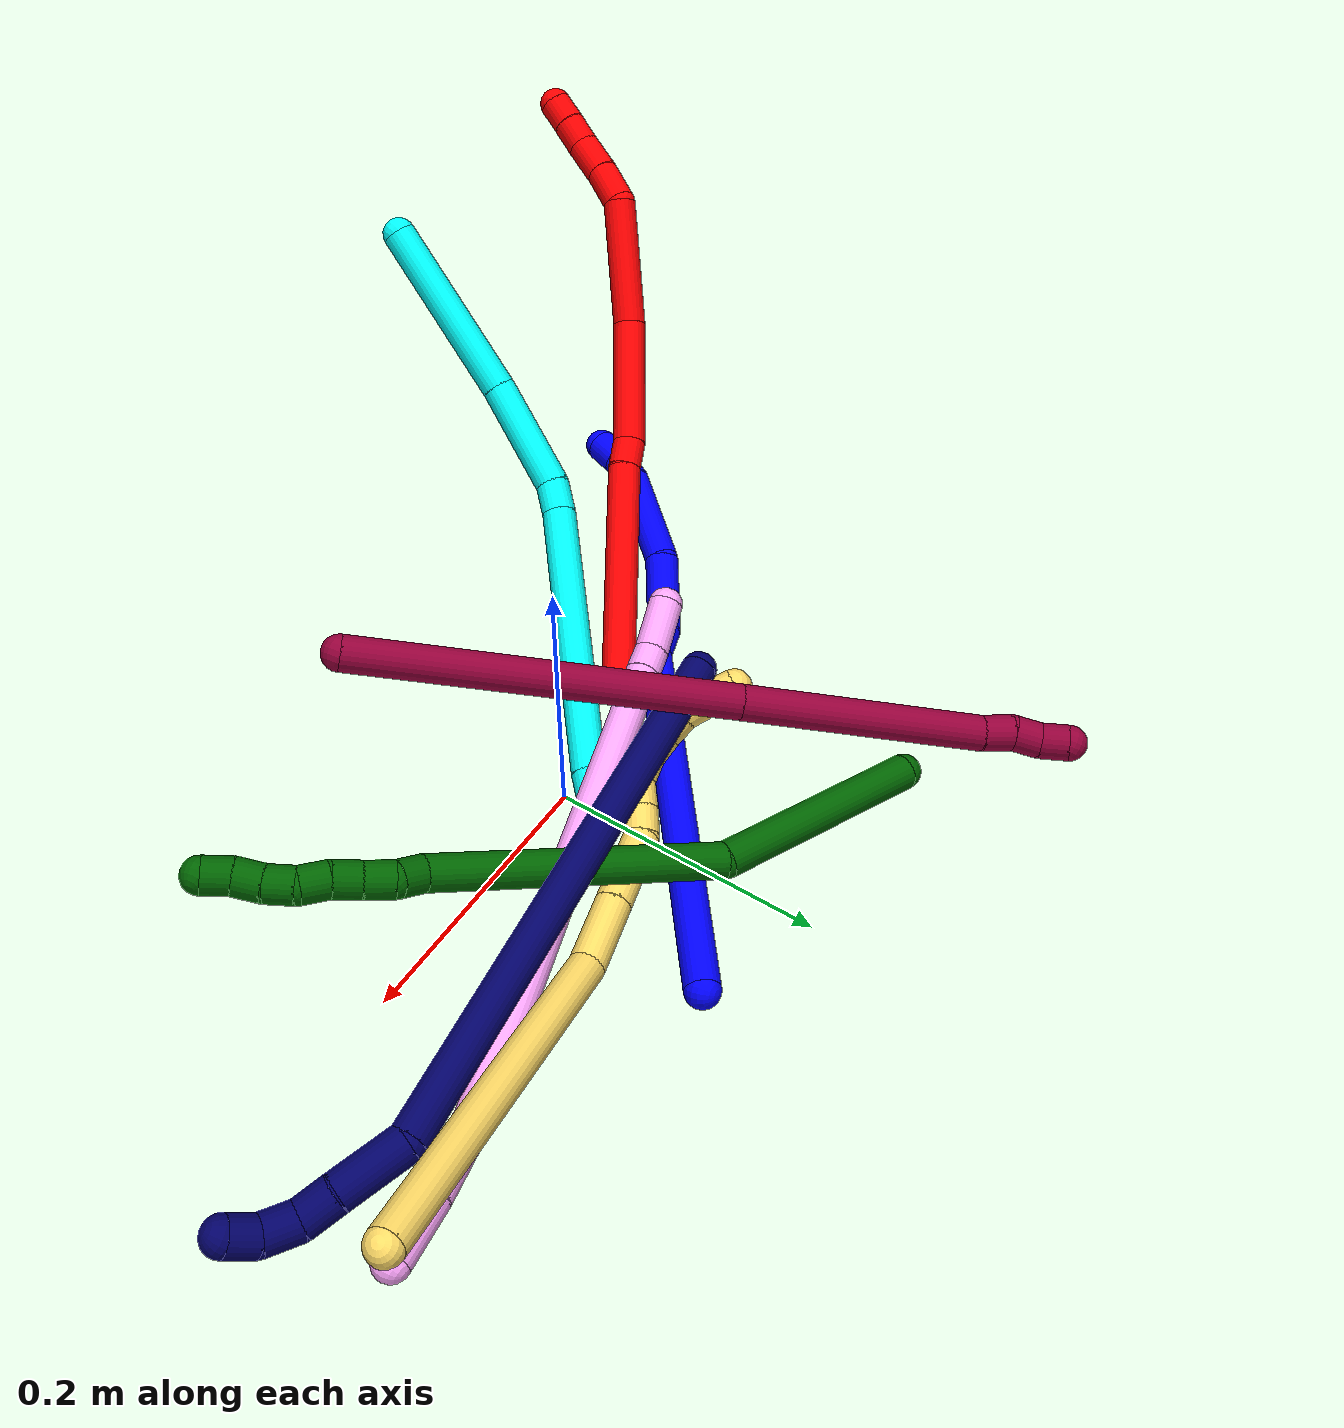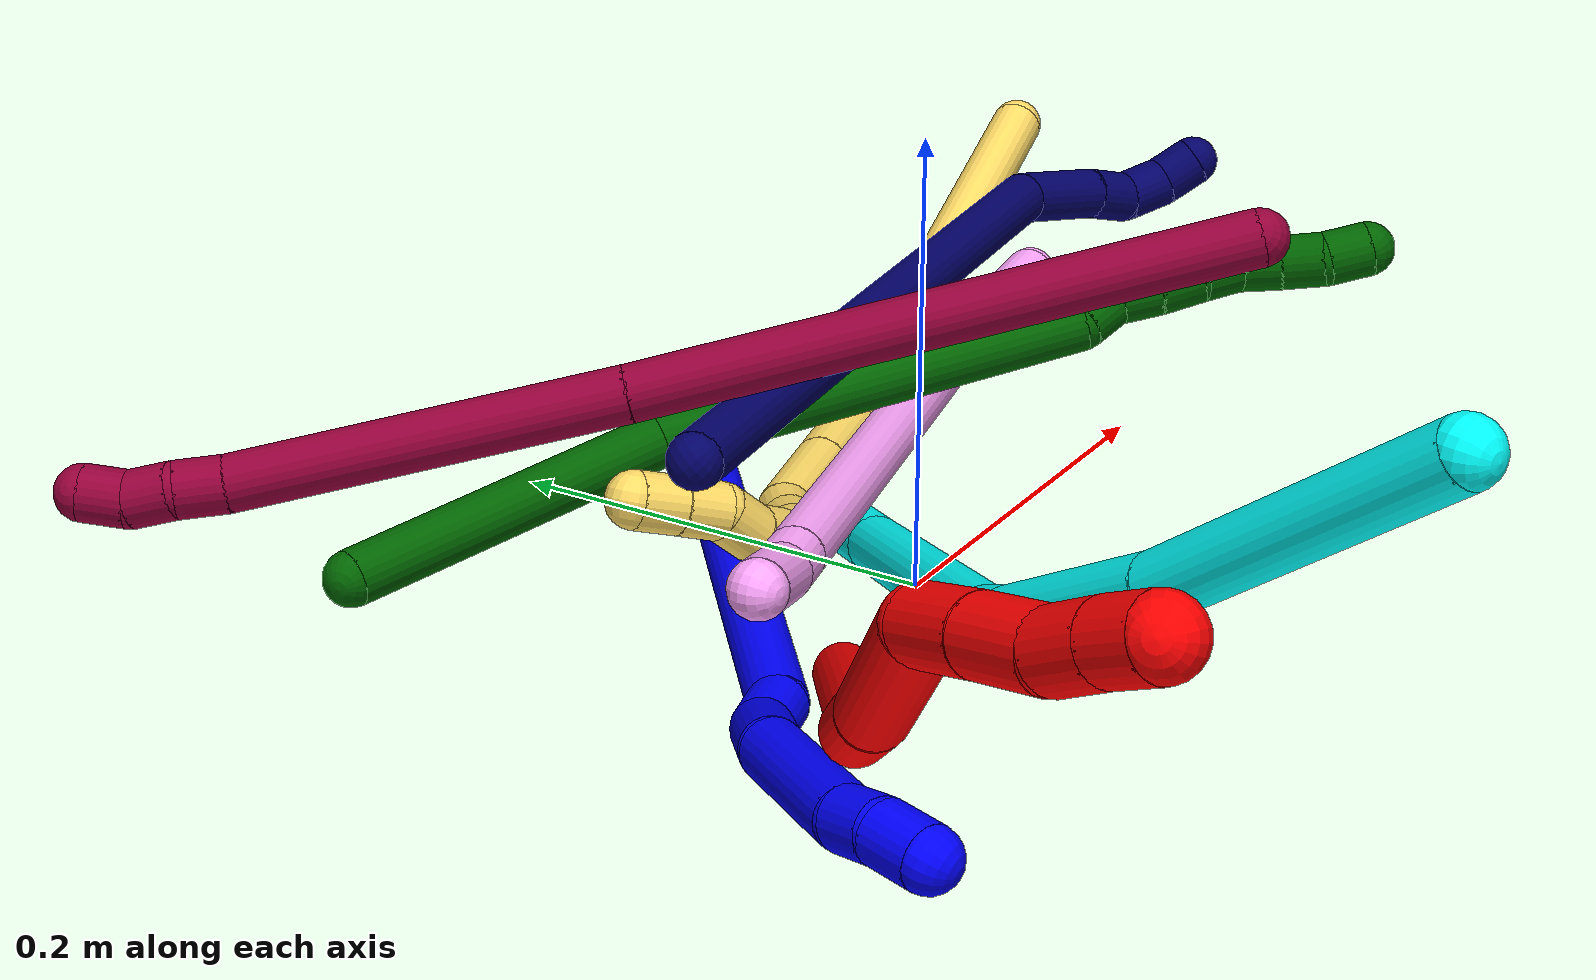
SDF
<sdf version="1.7">
 <world name="default">
  <plugin name="TubeGeneratorPlugin" filename="libtube_generator_plugin.so"/>
  <model name="photoneo_s_sensor">
   <static>1</static>
   <pose>0 0 2 1.57079 1.57079 3.14159</pose>
   <link name="link">
    <inertial><mass>0.1</mass></inertial>
    <sensor name="sensor" type="depth">
     <update_rate>30</update_rate>
     <camera>
      <horizontal_fov>1.22</horizontal_fov>
      <image><width>1920</width><height>1200</height><format>B8G8R8</format></image>
      <clip><near>0.1</near><far>4</far></clip>
      <depth_camera><output>points</output></depth_camera>
     </camera>
     <plugin name="camera_plugin" filename="libgazebo_ros_depth_camera.so">
      <baseline>0.2</baseline>
      <alwaysOn>1</alwaysOn>
      <updateRate>0.0</updateRate>
      <cameraName>camera_ir</cameraName>
      <imageTopicName>/camera/color/image_raw</imageTopicName>
      <cameraInfoTopicName>/camera/color/camera_info</cameraInfoTopicName>
      <depthImageTopicName>/camera/depth/image_raw</depthImageTopicName>
      <depthImageCameraInfoTopicName>/camera/depth/camera_info</depthImageCameraInfoTopicName>
      <pointCloudTopicName>/camera/depth/points</pointCloudTopicName>
      <frameName>fr_optical</frameName>
      <pointCloudCutoff>0.1</pointCloudCutoff>
      <pointCloudCutoffMax>2.0</pointCloudCutoffMax>
      <distortionK1>0</distortionK1>
      <distortionK2>0</distortionK2>
      <distortionK3>0</distortionK3>
      <distortionT1>0</distortionT1>
      <distortionT2>0</distortionT2>
      <CxPrime>0</CxPrime>
      <Cx>0</Cx>
      <Cy>0</Cy>
      <focalLength>0</focalLength>
      <hackBaseline>0</hackBaseline>
     </plugin>
    </sensor>
   </link>
  </model>
  <gravity>0 0 -9.8</gravity>
  <magnetic_field>6e-06 2.3e-05 -4.2e-05</magnetic_field>
  <atmosphere type="adiabatic"/>
  <physics name="default_physics" default="0" type="ode">
   <max_step_size>0.003</max_step_size>
   <real_time_factor>1</real_time_factor>
   <real_time_update_rate>1000</real_time_update_rate>
   <max_contacts>10000</max_contacts>
   <ode>
    <solver>
     <type>quick</type>
     <iters>100</iters>
     <sor>1.3</sor>
     <use_dynamic_moi_rescaling>0</use_dynamic_moi_rescaling>
    </solver>
    <constraints>
     <contact_max_correcting_vel>0</contact_max_correcting_vel>
     <contact_surface_layer>0.001</contact_surface_layer>
     <cfm>0</cfm>
     <erp>0.2</erp>
    </constraints>
   </ode>
  </physics>
  <scene><ambient>0.4 0.4 0.4 1</ambient><background>0.7 0.7 0.7 1</background><shadows>0</shadows></scene>
  <audio><device>default</device></audio>
  <spherical_coordinates>
   <surface_model>EARTH_WGS84</surface_model>
   <latitude_deg>0</latitude_deg>
   <longitude_deg>0</longitude_deg>
   <elevation>0</elevation>
   <heading_deg>0</heading_deg>
  </spherical_coordinates>
  <model name="bin">
   <static>1</static>
   <link name="bottom">
    <collision name="collision-bottom">
     <pose>0 0 -0.01 0 -0 0</pose>
     <geometry><box><size>0.8 0.6 0.02</size></box></geometry>
     <surface>
      <friction><ode><mu>100</mu><mu2>100</mu2></ode></friction>
      <contact><collide_bitmask>65535</collide_bitmask></contact>
     </surface>
    </collision>
   </link>
   <link name="west_wall">
    <collision name="collision-west_wall">
     <pose>-0.41 0 0.1 0 -0 0</pose>
     <geometry><box><size>0.02 0.6 0.2</size></box></geometry>
     <surface>
      <friction><ode><mu>100</mu><mu2>100</mu2></ode></friction>
      <contact><collide_bitmask>65535</collide_bitmask></contact>
     </surface>
    </collision>
   </link>
   <link name="east_wall">
    <collision name="collision-east_wall">
     <pose>0.41 0 0.1 0 -0 0</pose>
     <geometry><box><size>0.02 0.6 0.2</size></box></geometry>
     <surface>
      <friction><ode><mu>100</mu><mu2>100</mu2></ode></friction>
      <contact><collide_bitmask>65535</collide_bitmask></contact>
     </surface>
    </collision>
   </link>
   <link name="south_wall">
    <collision name="collision-south_wall">
     <pose>0 -0.31 0.1 0 -0 0</pose>
     <geometry><box><size>0.8 0.02 0.2</size></box></geometry>
     <surface>
      <friction><ode><mu>100</mu><mu2>100</mu2></ode></friction>
      <contact><collide_bitmask>65535</collide_bitmask></contact>
     </surface>
    </collision>
   </link>
   <link name="north_wall">
    <collision name="collision-north_wall">
     <pose>0 0.31 0.1 0 -0 0</pose>
     <geometry><box><size>0.8 0.02 0.2</size></box></geometry>
     <surface>
      <friction><ode><mu>100</mu><mu2>100</mu2></ode></friction>
      <contact><collide_bitmask>65535</collide_bitmask></contact>
     </surface>
    </collision>
   </link>
  </model>
  <model name="1">
   <static>0</static>
   <link name="1">
    <collision name="collision-cylinder-e_1_1_4">
     <pose>-0.094525 -0.068926 0.08705 0.669722 -0.705259 -0.254724</pose>
     <geometry><cylinder><radius>0.0125</radius><length>0.291639</length></cylinder></geometry>
     <surface>
      <friction><ode><mu>1.16</mu><mu2>1.16</mu2><slip1>0</slip1><slip2>0</slip2></ode></friction>
      <contact><ode><kp>1e+06</kp><kd>1</kd><max_vel>0</max_vel><min_depth>0.001</min_depth></ode></contact>
     </surface>
    </collision>
    <visual name="visual-cylinder-e_1_1_4">
     <pose>-0.094525 -0.068926 0.08705 0.669722 -0.705259 -0.254724</pose>
     <geometry><cylinder><radius>0.0125</radius><length>0.291639</length></cylinder></geometry>
     <material><ambient>0 0 1 1</ambient></material>
    </visual>
    <collision name="collision-cylinder-e_2_4_5">
     <pose>-0.198238 -0.145485 0.17708 1.19846 -0.842543 -0.594006</pose>
     <geometry><cylinder><radius>0.0125</radius><length>0.024623</length></cylinder></geometry>
     <surface>
      <friction><ode><mu>1.16</mu><mu2>1.16</mu2><slip1>0</slip1><slip2>0</slip2></ode></friction>
      <contact><ode><kp>1e+06</kp><kd>1</kd><max_vel>0</max_vel><min_depth>0.001</min_depth></ode></contact>
     </surface>
    </collision>
    <visual name="visual-cylinder-e_2_4_5">
     <pose>-0.198238 -0.145485 0.17708 1.19846 -0.842543 -0.594006</pose>
     <geometry><cylinder><radius>0.0125</radius><length>0.024623</length></cylinder></geometry>
     <material><ambient>0 0 1 1</ambient></material>
    </visual>
    <collision name="collision-cylinder-e_3_5_6">
     <pose>-0.233493 -0.160409 0.191876 0.552977 -1.08139 -0.33748</pose>
     <geometry><cylinder><radius>0.0125</radius><length>0.059067</length></cylinder></geometry>
     <surface>
      <friction><ode><mu>1.16</mu><mu2>1.16</mu2><slip1>0</slip1><slip2>0</slip2></ode></friction>
      <contact><ode><kp>1e+06</kp><kd>1</kd><max_vel>0</max_vel><min_depth>0.001</min_depth></ode></contact>
     </surface>
    </collision>
    <visual name="visual-cylinder-e_3_5_6">
     <pose>-0.233493 -0.160409 0.191876 0.552977 -1.08139 -0.33748</pose>
     <geometry><cylinder><radius>0.0125</radius><length>0.059067</length></cylinder></geometry>
     <material><ambient>0 0 1 1</ambient></material>
    </visual>
    <collision name="collision-cylinder-e_4_6_7">
     <pose>-0.288019 -0.176665 0.230243 0.325569 -0.793081 -0.137323</pose>
     <geometry><cylinder><radius>0.0125</radius><length>0.079884</length></cylinder></geometry>
     <surface>
      <friction><ode><mu>1.16</mu><mu2>1.16</mu2><slip1>0</slip1><slip2>0</slip2></ode></friction>
      <contact><ode><kp>1e+06</kp><kd>1</kd><max_vel>0</max_vel><min_depth>0.001</min_depth></ode></contact>
     </surface>
    </collision>
    <visual name="visual-cylinder-e_4_6_7">
     <pose>-0.288019 -0.176665 0.230243 0.325569 -0.793081 -0.137323</pose>
     <geometry><cylinder><radius>0.0125</radius><length>0.079884</length></cylinder></geometry>
     <material><ambient>0 0 1 1</ambient></material>
    </visual>
    <collision name="collision-cylinder-e_5_7_8">
     <pose>-0.323547 -0.185663 0.265273 0.004011 -0.695082 -0.001453</pose>
     <geometry><cylinder><radius>0.0125</radius><length>0.022073</length></cylinder></geometry>
     <surface>
      <friction><ode><mu>1.16</mu><mu2>1.16</mu2><slip1>0</slip1><slip2>0</slip2></ode></friction>
      <contact><ode><kp>1e+06</kp><kd>1</kd><max_vel>0</max_vel><min_depth>0.001</min_depth></ode></contact>
     </surface>
    </collision>
    <visual name="visual-cylinder-e_5_7_8">
     <pose>-0.323547 -0.185663 0.265273 0.004011 -0.695082 -0.001453</pose>
     <geometry><cylinder><radius>0.0125</radius><length>0.022073</length></cylinder></geometry>
     <material><ambient>0 0 1 1</ambient></material>
    </visual>
    <collision name="collision-cylinder-e_6_8_2">
     <pose>-0.335471 -0.18653 0.283981 0.081236 -0.441825 -0.018253</pose>
     <geometry><cylinder><radius>0.0125</radius><length>0.022714</length></cylinder></geometry>
     <surface>
      <friction><ode><mu>1.16</mu><mu2>1.16</mu2><slip1>0</slip1><slip2>0</slip2></ode></friction>
      <contact><ode><kp>1e+06</kp><kd>1</kd><max_vel>0</max_vel><min_depth>0.001</min_depth></ode></contact>
     </surface>
    </collision>
    <visual name="visual-cylinder-e_6_8_2">
     <pose>-0.335471 -0.18653 0.283981 0.081236 -0.441825 -0.018253</pose>
     <geometry><cylinder><radius>0.0125</radius><length>0.022714</length></cylinder></geometry>
     <material><ambient>0 0 1 1</ambient></material>
    </visual>
    <collision name="collision-sphere-2">
     <pose>-0.340327 -0.187363 0.294214 0 -0 0</pose>
     <geometry><sphere><radius>0.0125</radius></sphere></geometry>
     <surface>
      <friction><ode><mu>1.16</mu><mu2>1.16</mu2><slip1>0</slip1><slip2>0</slip2></ode></friction>
      <contact><ode><kp>1e+06</kp><kd>1</kd><max_vel>0</max_vel><min_depth>0.001</min_depth></ode></contact>
     </surface>
    </collision>
    <visual name="visual-sphere-2">
     <pose>-0.340327 -0.187363 0.294214 0 -0 0</pose>
     <geometry><sphere><radius>0.0125</radius></sphere></geometry>
     <material><ambient>0 0 1 1</ambient></material>
    </visual>
    <collision name="collision-sphere-4">
     <pose>-0.189049 -0.137852 0.174099 0 -0 0</pose>
     <geometry><sphere><radius>0.0125</radius></sphere></geometry>
     <surface>
      <friction><ode><mu>1.16</mu><mu2>1.16</mu2><slip1>0</slip1><slip2>0</slip2></ode></friction>
      <contact><ode><kp>1e+06</kp><kd>1</kd><max_vel>0</max_vel><min_depth>0.001</min_depth></ode></contact>
     </surface>
    </collision>
    <visual name="visual-sphere-4">
     <pose>-0.189049 -0.137852 0.174099 0 -0 0</pose>
     <geometry><sphere><radius>0.0125</radius></sphere></geometry>
     <material><ambient>0 0 1 1</ambient></material>
    </visual>
    <collision name="collision-sphere-1">
     <geometry><sphere><radius>0.0125</radius></sphere></geometry>
     <surface>
      <friction><ode><mu>1.16</mu><mu2>1.16</mu2><slip1>0</slip1><slip2>0</slip2></ode></friction>
      <contact><ode><kp>1e+06</kp><kd>1</kd><max_vel>0</max_vel><min_depth>0.001</min_depth></ode></contact>
     </surface>
    </collision>
    <visual name="visual-sphere-1">
     <geometry><sphere><radius>0.0125</radius></sphere></geometry>
     <material><ambient>0 0 1 1</ambient></material>
    </visual>
    <collision name="collision-sphere-8">
     <pose>-0.330615 -0.185697 0.273749 0 -0 0</pose>
     <geometry><sphere><radius>0.0125</radius></sphere></geometry>
     <surface>
      <friction><ode><mu>1.16</mu><mu2>1.16</mu2><slip1>0</slip1><slip2>0</slip2></ode></friction>
      <contact><ode><kp>1e+06</kp><kd>1</kd><max_vel>0</max_vel><min_depth>0.001</min_depth></ode></contact>
     </surface>
    </collision>
    <visual name="visual-sphere-8">
     <pose>-0.330615 -0.185697 0.273749 0 -0 0</pose>
     <geometry><sphere><radius>0.0125</radius></sphere></geometry>
     <material><ambient>0 0 1 1</ambient></material>
    </visual>
    <collision name="collision-sphere-5">
     <pose>-0.207427 -0.153117 0.180061 0 -0 0</pose>
     <geometry><sphere><radius>0.0125</radius></sphere></geometry>
     <surface>
      <friction><ode><mu>1.16</mu><mu2>1.16</mu2><slip1>0</slip1><slip2>0</slip2></ode></friction>
      <contact><ode><kp>1e+06</kp><kd>1</kd><max_vel>0</max_vel><min_depth>0.001</min_depth></ode></contact>
     </surface>
    </collision>
    <visual name="visual-sphere-5">
     <pose>-0.207427 -0.153117 0.180061 0 -0 0</pose>
     <geometry><sphere><radius>0.0125</radius></sphere></geometry>
     <material><ambient>0 0 1 1</ambient></material>
    </visual>
    <collision name="collision-sphere-6">
     <pose>-0.25956 -0.167701 0.20369 0 -0 0</pose>
     <geometry><sphere><radius>0.0125</radius></sphere></geometry>
     <surface>
      <friction><ode><mu>1.16</mu><mu2>1.16</mu2><slip1>0</slip1><slip2>0</slip2></ode></friction>
      <contact><ode><kp>1e+06</kp><kd>1</kd><max_vel>0</max_vel><min_depth>0.001</min_depth></ode></contact>
     </surface>
    </collision>
    <visual name="visual-sphere-6">
     <pose>-0.25956 -0.167701 0.20369 0 -0 0</pose>
     <geometry><sphere><radius>0.0125</radius></sphere></geometry>
     <material><ambient>0 0 1 1</ambient></material>
    </visual>
    <collision name="collision-sphere-7">
     <pose>-0.316479 -0.185629 0.256797 0 -0 0</pose>
     <geometry><sphere><radius>0.0125</radius></sphere></geometry>
     <surface>
      <friction><ode><mu>1.16</mu><mu2>1.16</mu2><slip1>0</slip1><slip2>0</slip2></ode></friction>
      <contact><ode><kp>1e+06</kp><kd>1</kd><max_vel>0</max_vel><min_depth>0.001</min_depth></ode></contact>
     </surface>
    </collision>
    <visual name="visual-sphere-7">
     <pose>-0.316479 -0.185629 0.256797 0 -0 0</pose>
     <geometry><sphere><radius>0.0125</radius></sphere></geometry>
     <material><ambient>0 0 1 1</ambient></material>
    </visual>
    <inertial>
     <pose>-0.168019 -0.111213 0.143559 0 -0 0</pose>
     <mass>0.5</mass>
     <inertia>
      <ixx>0.001143</ixx>
      <ixy>0</ixy>
      <ixz>0</ixz>
      <iyy>0.001434</iyy>
      <iyz>0</iyz>
      <izz>0.002423</izz>
     </inertia>
    </inertial>
   </link>
   <pose>0.086305 0.168958 0.011499 1.98727 0.80471 0.323793</pose>
  </model>
  <model name="2">
   <static>0</static>
   <link name="2">
    <collision name="collision-cylinder-e_1_1_4">
     <pose>-0.020642 -0.007732 0.083497 0.092337 -0.241371 -0.011206</pose>
     <geometry><cylinder><radius>0.0125</radius><length>0.172715</length></cylinder></geometry>
     <surface>
      <friction><ode><mu>1.16</mu><mu2>1.16</mu2><slip1>0</slip1><slip2>0</slip2></ode></friction>
      <contact><ode><kp>1e+06</kp><kd>1</kd><max_vel>0</max_vel><min_depth>0.001</min_depth></ode></contact>
     </surface>
    </collision>
    <visual name="visual-cylinder-e_1_1_4">
     <pose>-0.020642 -0.007732 0.083497 0.092337 -0.241371 -0.011206</pose>
     <geometry><cylinder><radius>0.0125</radius><length>0.172715</length></cylinder></geometry>
     <material><ambient>1 0 0 1</ambient></material>
    </visual>
    <collision name="collision-cylinder-e_2_4_5">
     <pose>-0.04294 -0.015278 0.178597 -0.015965 -0.141639 0.001133</pose>
     <geometry><cylinder><radius>0.0125</radius><length>0.023446</length></cylinder></geometry>
     <surface>
      <friction><ode><mu>1.16</mu><mu2>1.16</mu2><slip1>0</slip1><slip2>0</slip2></ode></friction>
      <contact><ode><kp>1e+06</kp><kd>1</kd><max_vel>0</max_vel><min_depth>0.001</min_depth></ode></contact>
     </surface>
    </collision>
    <visual name="visual-cylinder-e_2_4_5">
     <pose>-0.04294 -0.015278 0.178597 -0.015965 -0.141639 0.001133</pose>
     <geometry><cylinder><radius>0.0125</radius><length>0.023446</length></cylinder></geometry>
     <material><ambient>1 0 0 1</ambient></material>
    </visual>
    <collision name="collision-cylinder-e_3_5_6">
     <pose>-0.05367 -0.027262 0.23691 0.254862 -0.185852 -0.02388</pose>
     <geometry><cylinder><radius>0.0125</radius><length>0.098227</length></cylinder></geometry>
     <surface>
      <friction><ode><mu>1.16</mu><mu2>1.16</mu2><slip1>0</slip1><slip2>0</slip2></ode></friction>
      <contact><ode><kp>1e+06</kp><kd>1</kd><max_vel>0</max_vel><min_depth>0.001</min_depth></ode></contact>
     </surface>
    </collision>
    <visual name="visual-cylinder-e_3_5_6">
     <pose>-0.05367 -0.027262 0.23691 0.254862 -0.185852 -0.02388</pose>
     <geometry><cylinder><radius>0.0125</radius><length>0.098227</length></cylinder></geometry>
     <material><ambient>1 0 0 1</ambient></material>
    </visual>
    <collision name="collision-cylinder-e_4_6_7">
     <pose>-0.071015 -0.060711 0.327048 0.455612 -0.169361 -0.039352</pose>
     <geometry><cylinder><radius>0.0125</radius><length>0.09813</length></cylinder></geometry>
     <surface>
      <friction><ode><mu>1.16</mu><mu2>1.16</mu2><slip1>0</slip1><slip2>0</slip2></ode></friction>
      <contact><ode><kp>1e+06</kp><kd>1</kd><max_vel>0</max_vel><min_depth>0.001</min_depth></ode></contact>
     </surface>
    </collision>
    <visual name="visual-cylinder-e_4_6_7">
     <pose>-0.071015 -0.060711 0.327048 0.455612 -0.169361 -0.039352</pose>
     <geometry><cylinder><radius>0.0125</radius><length>0.09813</length></cylinder></geometry>
     <material><ambient>1 0 0 1</ambient></material>
    </visual>
    <collision name="collision-cylinder-e_5_7_8">
     <pose>-0.089216 -0.085732 0.382378 0.304543 -0.672313 -0.10714</pose>
     <geometry><cylinder><radius>0.0125</radius><length>0.031889</length></cylinder></geometry>
     <surface>
      <friction><ode><mu>1.16</mu><mu2>1.16</mu2><slip1>0</slip1><slip2>0</slip2></ode></friction>
      <contact><ode><kp>1e+06</kp><kd>1</kd><max_vel>0</max_vel><min_depth>0.001</min_depth></ode></contact>
     </surface>
    </collision>
    <visual name="visual-cylinder-e_5_7_8">
     <pose>-0.089216 -0.085732 0.382378 0.304543 -0.672313 -0.10714</pose>
     <geometry><cylinder><radius>0.0125</radius><length>0.031889</length></cylinder></geometry>
     <material><ambient>1 0 0 1</ambient></material>
    </visual>
    <collision name="collision-cylinder-e_6_8_9">
     <pose>-0.109859 -0.092908 0.405238 0.303796 -0.750654 -0.12048</pose>
     <geometry><cylinder><radius>0.0125</radius><length>0.031411</length></cylinder></geometry>
     <surface>
      <friction><ode><mu>1.16</mu><mu2>1.16</mu2><slip1>0</slip1><slip2>0</slip2></ode></friction>
      <contact><ode><kp>1e+06</kp><kd>1</kd><max_vel>0</max_vel><min_depth>0.001</min_depth></ode></contact>
     </surface>
    </collision>
    <visual name="visual-cylinder-e_6_8_9">
     <pose>-0.109859 -0.092908 0.405238 0.303796 -0.750654 -0.12048</pose>
     <geometry><cylinder><radius>0.0125</radius><length>0.031411</length></cylinder></geometry>
     <material><ambient>1 0 0 1</ambient></material>
    </visual>
    <collision name="collision-cylinder-e_7_9_10">
     <pose>-0.127545 -0.101467 0.4239 0.586844 -0.645927 -0.201559</pose>
     <geometry><cylinder><radius>0.0125</radius><length>0.02317</length></cylinder></geometry>
     <surface>
      <friction><ode><mu>1.16</mu><mu2>1.16</mu2><slip1>0</slip1><slip2>0</slip2></ode></friction>
      <contact><ode><kp>1e+06</kp><kd>1</kd><max_vel>0</max_vel><min_depth>0.001</min_depth></ode></contact>
     </surface>
    </collision>
    <visual name="visual-cylinder-e_7_9_10">
     <pose>-0.127545 -0.101467 0.4239 0.586844 -0.645927 -0.201559</pose>
     <geometry><cylinder><radius>0.0125</radius><length>0.02317</length></cylinder></geometry>
     <material><ambient>1 0 0 1</ambient></material>
    </visual>
    <collision name="collision-cylinder-e_8_10_2">
     <pose>-0.141103 -0.110845 0.438598 0.546604 -0.677259 -0.196815</pose>
     <geometry><cylinder><radius>0.0125</radius><length>0.021012</length></cylinder></geometry>
     <surface>
      <friction><ode><mu>1.16</mu><mu2>1.16</mu2><slip1>0</slip1><slip2>0</slip2></ode></friction>
      <contact><ode><kp>1e+06</kp><kd>1</kd><max_vel>0</max_vel><min_depth>0.001</min_depth></ode></contact>
     </surface>
    </collision>
    <visual name="visual-cylinder-e_8_10_2">
     <pose>-0.141103 -0.110845 0.438598 0.546604 -0.677259 -0.196815</pose>
     <geometry><cylinder><radius>0.0125</radius><length>0.021012</length></cylinder></geometry>
     <material><ambient>1 0 0 1</ambient></material>
    </visual>
    <collision name="collision-sphere-2">
     <pose>-0.147686 -0.115101 0.445592 0 -0 0</pose>
     <geometry><sphere><radius>0.0125</radius></sphere></geometry>
     <surface>
      <friction><ode><mu>1.16</mu><mu2>1.16</mu2><slip1>0</slip1><slip2>0</slip2></ode></friction>
      <contact><ode><kp>1e+06</kp><kd>1</kd><max_vel>0</max_vel><min_depth>0.001</min_depth></ode></contact>
     </surface>
    </collision>
    <visual name="visual-sphere-2">
     <pose>-0.147686 -0.115101 0.445592 0 -0 0</pose>
     <geometry><sphere><radius>0.0125</radius></sphere></geometry>
     <material><ambient>1 0 0 1</ambient></material>
    </visual>
    <collision name="collision-sphere-10">
     <pose>-0.134519 -0.106589 0.431604 0 -0 0</pose>
     <geometry><sphere><radius>0.0125</radius></sphere></geometry>
     <surface>
      <friction><ode><mu>1.16</mu><mu2>1.16</mu2><slip1>0</slip1><slip2>0</slip2></ode></friction>
      <contact><ode><kp>1e+06</kp><kd>1</kd><max_vel>0</max_vel><min_depth>0.001</min_depth></ode></contact>
     </surface>
    </collision>
    <visual name="visual-sphere-10">
     <pose>-0.134519 -0.106589 0.431604 0 -0 0</pose>
     <geometry><sphere><radius>0.0125</radius></sphere></geometry>
     <material><ambient>1 0 0 1</ambient></material>
    </visual>
    <collision name="collision-sphere-9">
     <pose>-0.120572 -0.096344 0.416197 0 -0 0</pose>
     <geometry><sphere><radius>0.0125</radius></sphere></geometry>
     <surface>
      <friction><ode><mu>1.16</mu><mu2>1.16</mu2><slip1>0</slip1><slip2>0</slip2></ode></friction>
      <contact><ode><kp>1e+06</kp><kd>1</kd><max_vel>0</max_vel><min_depth>0.001</min_depth></ode></contact>
     </surface>
    </collision>
    <visual name="visual-sphere-9">
     <pose>-0.120572 -0.096344 0.416197 0 -0 0</pose>
     <geometry><sphere><radius>0.0125</radius></sphere></geometry>
     <material><ambient>1 0 0 1</ambient></material>
    </visual>
    <collision name="collision-sphere-4">
     <pose>-0.041285 -0.015464 0.166993 0 -0 0</pose>
     <geometry><sphere><radius>0.0125</radius></sphere></geometry>
     <surface>
      <friction><ode><mu>1.16</mu><mu2>1.16</mu2><slip1>0</slip1><slip2>0</slip2></ode></friction>
      <contact><ode><kp>1e+06</kp><kd>1</kd><max_vel>0</max_vel><min_depth>0.001</min_depth></ode></contact>
     </surface>
    </collision>
    <visual name="visual-sphere-4">
     <pose>-0.041285 -0.015464 0.166993 0 -0 0</pose>
     <geometry><sphere><radius>0.0125</radius></sphere></geometry>
     <material><ambient>1 0 0 1</ambient></material>
    </visual>
    <collision name="collision-sphere-1">
     <geometry><sphere><radius>0.0125</radius></sphere></geometry>
     <surface>
      <friction><ode><mu>1.16</mu><mu2>1.16</mu2><slip1>0</slip1><slip2>0</slip2></ode></friction>
      <contact><ode><kp>1e+06</kp><kd>1</kd><max_vel>0</max_vel><min_depth>0.001</min_depth></ode></contact>
     </surface>
    </collision>
    <visual name="visual-sphere-1">
     <geometry><sphere><radius>0.0125</radius></sphere></geometry>
     <material><ambient>1 0 0 1</ambient></material>
    </visual>
    <collision name="collision-sphere-8">
     <pose>-0.099146 -0.089473 0.394279 0 -0 0</pose>
     <geometry><sphere><radius>0.0125</radius></sphere></geometry>
     <surface>
      <friction><ode><mu>1.16</mu><mu2>1.16</mu2><slip1>0</slip1><slip2>0</slip2></ode></friction>
      <contact><ode><kp>1e+06</kp><kd>1</kd><max_vel>0</max_vel><min_depth>0.001</min_depth></ode></contact>
     </surface>
    </collision>
    <visual name="visual-sphere-8">
     <pose>-0.099146 -0.089473 0.394279 0 -0 0</pose>
     <geometry><sphere><radius>0.0125</radius></sphere></geometry>
     <material><ambient>1 0 0 1</ambient></material>
    </visual>
    <collision name="collision-sphere-5">
     <pose>-0.044595 -0.015093 0.190202 0 -0 0</pose>
     <geometry><sphere><radius>0.0125</radius></sphere></geometry>
     <surface>
      <friction><ode><mu>1.16</mu><mu2>1.16</mu2><slip1>0</slip1><slip2>0</slip2></ode></friction>
      <contact><ode><kp>1e+06</kp><kd>1</kd><max_vel>0</max_vel><min_depth>0.001</min_depth></ode></contact>
     </surface>
    </collision>
    <visual name="visual-sphere-5">
     <pose>-0.044595 -0.015093 0.190202 0 -0 0</pose>
     <geometry><sphere><radius>0.0125</radius></sphere></geometry>
     <material><ambient>1 0 0 1</ambient></material>
    </visual>
    <collision name="collision-sphere-6">
     <pose>-0.062745 -0.039431 0.283618 0 -0 0</pose>
     <geometry><sphere><radius>0.0125</radius></sphere></geometry>
     <surface>
      <friction><ode><mu>1.16</mu><mu2>1.16</mu2><slip1>0</slip1><slip2>0</slip2></ode></friction>
      <contact><ode><kp>1e+06</kp><kd>1</kd><max_vel>0</max_vel><min_depth>0.001</min_depth></ode></contact>
     </surface>
    </collision>
    <visual name="visual-sphere-6">
     <pose>-0.062745 -0.039431 0.283618 0 -0 0</pose>
     <geometry><sphere><radius>0.0125</radius></sphere></geometry>
     <material><ambient>1 0 0 1</ambient></material>
    </visual>
    <collision name="collision-sphere-7">
     <pose>-0.079285 -0.081992 0.370478 0 -0 0</pose>
     <geometry><sphere><radius>0.0125</radius></sphere></geometry>
     <surface>
      <friction><ode><mu>1.16</mu><mu2>1.16</mu2><slip1>0</slip1><slip2>0</slip2></ode></friction>
      <contact><ode><kp>1e+06</kp><kd>1</kd><max_vel>0</max_vel><min_depth>0.001</min_depth></ode></contact>
     </surface>
    </collision>
    <visual name="visual-sphere-7">
     <pose>-0.079285 -0.081992 0.370478 0 -0 0</pose>
     <geometry><sphere><radius>0.0125</radius></sphere></geometry>
     <material><ambient>1 0 0 1</ambient></material>
    </visual>
    <inertial>
     <pose>-0.058057 -0.041323 0.235866 0 -0 0</pose>
     <mass>0.5</mass>
     <inertia>
      <ixx>0.000574</ixx>
      <ixy>0</ixy>
      <ixz>0</ixz>
      <iyy>0.000581</iyy>
      <iyz>0</iyz>
      <izz>0.000274</izz>
     </inertia>
    </inertial>
   </link>
   <pose>-0.104401 -0.025162 0.011535 -1.15652 -0.284355 1.72975</pose>
  </model>
  <model name="3">
   <static>0</static>
   <link name="3">
    <collision name="collision-cylinder-e_1_1_4">
     <pose>0.040071 0.000463 -0.057289 -3.13351 0.610347 -3.11593</pose>
     <geometry><cylinder><radius>0.0125</radius><length>0.139827</length></cylinder></geometry>
     <surface>
      <friction><ode><mu>1.16</mu><mu2>1.16</mu2><slip1>0</slip1><slip2>0</slip2></ode></friction>
      <contact><ode><kp>1e+06</kp><kd>1</kd><max_vel>0</max_vel><min_depth>0.001</min_depth></ode></contact>
     </surface>
    </collision>
    <visual name="visual-cylinder-e_1_1_4">
     <pose>0.040071 0.000463 -0.057289 -3.13351 0.610347 -3.11593</pose>
     <geometry><cylinder><radius>0.0125</radius><length>0.139827</length></cylinder></geometry>
     <material><ambient>0.003922 1 0.996078 1</ambient></material>
    </visual>
    <collision name="collision-cylinder-e_2_4_5">
     <pose>0.099858 0.005992 -0.152269 -3.008 0.478276 -2.60602</pose>
     <geometry><cylinder><radius>0.0125</radius><length>0.085675</length></cylinder></geometry>
     <surface>
      <friction><ode><mu>1.16</mu><mu2>1.16</mu2><slip1>0</slip1><slip2>0</slip2></ode></friction>
      <contact><ode><kp>1e+06</kp><kd>1</kd><max_vel>0</max_vel><min_depth>0.001</min_depth></ode></contact>
     </surface>
    </collision>
    <visual name="visual-cylinder-e_2_4_5">
     <pose>0.099858 0.005992 -0.152269 -3.008 0.478276 -2.60602</pose>
     <geometry><cylinder><radius>0.0125</radius><length>0.085675</length></cylinder></geometry>
     <material><ambient>0.003922 1 0.996078 1</ambient></material>
    </visual>
    <collision name="collision-cylinder-e_3_5_6">
     <pose>0.123813 0.016175 -0.200367 -2.68455 0.350474 -1.30131</pose>
     <geometry><cylinder><radius>0.0125</radius><length>0.024696</length></cylinder></geometry>
     <surface>
      <friction><ode><mu>1.16</mu><mu2>1.16</mu2><slip1>0</slip1><slip2>0</slip2></ode></friction>
      <contact><ode><kp>1e+06</kp><kd>1</kd><max_vel>0</max_vel><min_depth>0.001</min_depth></ode></contact>
     </surface>
    </collision>
    <visual name="visual-cylinder-e_3_5_6">
     <pose>0.123813 0.016175 -0.200367 -2.68455 0.350474 -1.30131</pose>
     <geometry><cylinder><radius>0.0125</radius><length>0.024696</length></cylinder></geometry>
     <material><ambient>0.003922 1 0.996078 1</ambient></material>
    </visual>
    <collision name="collision-cylinder-e_4_6_7">
     <pose>0.151073 0.075208 -0.297197 -2.58381 0.222259 -0.743178</pose>
     <geometry><cylinder><radius>0.0125</radius><length>0.208861</length></cylinder></geometry>
     <surface>
      <friction><ode><mu>1.16</mu><mu2>1.16</mu2><slip1>0</slip1><slip2>0</slip2></ode></friction>
      <contact><ode><kp>1e+06</kp><kd>1</kd><max_vel>0</max_vel><min_depth>0.001</min_depth></ode></contact>
     </surface>
    </collision>
    <visual name="visual-cylinder-e_4_6_7">
     <pose>0.151073 0.075208 -0.297197 -2.58381 0.222259 -0.743178</pose>
     <geometry><cylinder><radius>0.0125</radius><length>0.208861</length></cylinder></geometry>
     <material><ambient>0.003922 1 0.996078 1</ambient></material>
    </visual>
    <collision name="collision-cylinder-e_5_7_2">
     <pose>0.177184 0.138073 -0.40177 -2.68354 0.151568 -0.629753</pose>
     <geometry><cylinder><radius>0.0125</radius><length>0.040942</length></cylinder></geometry>
     <surface>
      <friction><ode><mu>1.16</mu><mu2>1.16</mu2><slip1>0</slip1><slip2>0</slip2></ode></friction>
      <contact><ode><kp>1e+06</kp><kd>1</kd><max_vel>0</max_vel><min_depth>0.001</min_depth></ode></contact>
     </surface>
    </collision>
    <visual name="visual-cylinder-e_5_7_2">
     <pose>0.177184 0.138073 -0.40177 -2.68354 0.151568 -0.629753</pose>
     <geometry><cylinder><radius>0.0125</radius><length>0.040942</length></cylinder></geometry>
     <material><ambient>0.003922 1 0.996078 1</ambient></material>
    </visual>
    <collision name="collision-sphere-2">
     <pose>0.180274 0.147021 -0.41992 0 -0 0</pose>
     <geometry><sphere><radius>0.0125</radius></sphere></geometry>
     <surface>
      <friction><ode><mu>1.16</mu><mu2>1.16</mu2><slip1>0</slip1><slip2>0</slip2></ode></friction>
      <contact><ode><kp>1e+06</kp><kd>1</kd><max_vel>0</max_vel><min_depth>0.001</min_depth></ode></contact>
     </surface>
    </collision>
    <visual name="visual-sphere-2">
     <pose>0.180274 0.147021 -0.41992 0 -0 0</pose>
     <geometry><sphere><radius>0.0125</radius></sphere></geometry>
     <material><ambient>0.003922 1 0.996078 1</ambient></material>
    </visual>
    <collision name="collision-sphere-7">
     <pose>0.174093 0.129124 -0.38362 0 -0 0</pose>
     <geometry><sphere><radius>0.0125</radius></sphere></geometry>
     <surface>
      <friction><ode><mu>1.16</mu><mu2>1.16</mu2><slip1>0</slip1><slip2>0</slip2></ode></friction>
      <contact><ode><kp>1e+06</kp><kd>1</kd><max_vel>0</max_vel><min_depth>0.001</min_depth></ode></contact>
     </surface>
    </collision>
    <visual name="visual-sphere-7">
     <pose>0.174093 0.129124 -0.38362 0 -0 0</pose>
     <geometry><sphere><radius>0.0125</radius></sphere></geometry>
     <material><ambient>0.003922 1 0.996078 1</ambient></material>
    </visual>
    <collision name="collision-sphere-6">
     <pose>0.128053 0.021293 -0.210774 0 -0 0</pose>
     <geometry><sphere><radius>0.0125</radius></sphere></geometry>
     <surface>
      <friction><ode><mu>1.16</mu><mu2>1.16</mu2><slip1>0</slip1><slip2>0</slip2></ode></friction>
      <contact><ode><kp>1e+06</kp><kd>1</kd><max_vel>0</max_vel><min_depth>0.001</min_depth></ode></contact>
     </surface>
    </collision>
    <visual name="visual-sphere-6">
     <pose>0.128053 0.021293 -0.210774 0 -0 0</pose>
     <geometry><sphere><radius>0.0125</radius></sphere></geometry>
     <material><ambient>0.003922 1 0.996078 1</ambient></material>
    </visual>
    <collision name="collision-sphere-5">
     <pose>0.119574 0.011057 -0.18996 0 -0 0</pose>
     <geometry><sphere><radius>0.0125</radius></sphere></geometry>
     <surface>
      <friction><ode><mu>1.16</mu><mu2>1.16</mu2><slip1>0</slip1><slip2>0</slip2></ode></friction>
      <contact><ode><kp>1e+06</kp><kd>1</kd><max_vel>0</max_vel><min_depth>0.001</min_depth></ode></contact>
     </surface>
    </collision>
    <visual name="visual-sphere-5">
     <pose>0.119574 0.011057 -0.18996 0 -0 0</pose>
     <geometry><sphere><radius>0.0125</radius></sphere></geometry>
     <material><ambient>0.003922 1 0.996078 1</ambient></material>
    </visual>
    <collision name="collision-sphere-1">
     <geometry><sphere><radius>0.0125</radius></sphere></geometry>
     <surface>
      <friction><ode><mu>1.16</mu><mu2>1.16</mu2><slip1>0</slip1><slip2>0</slip2></ode></friction>
      <contact><ode><kp>1e+06</kp><kd>1</kd><max_vel>0</max_vel><min_depth>0.001</min_depth></ode></contact>
     </surface>
    </collision>
    <visual name="visual-sphere-1">
     <geometry><sphere><radius>0.0125</radius></sphere></geometry>
     <material><ambient>0.003922 1 0.996078 1</ambient></material>
    </visual>
    <collision name="collision-sphere-4">
     <pose>0.080142 0.000926 -0.114577 0 -0 0</pose>
     <geometry><sphere><radius>0.0125</radius></sphere></geometry>
     <surface>
      <friction><ode><mu>1.16</mu><mu2>1.16</mu2><slip1>0</slip1><slip2>0</slip2></ode></friction>
      <contact><ode><kp>1e+06</kp><kd>1</kd><max_vel>0</max_vel><min_depth>0.001</min_depth></ode></contact>
     </surface>
    </collision>
    <visual name="visual-sphere-4">
     <pose>0.080142 0.000926 -0.114577 0 -0 0</pose>
     <geometry><sphere><radius>0.0125</radius></sphere></geometry>
     <material><ambient>0.003922 1 0.996078 1</ambient></material>
    </visual>
    <inertial>
     <pose>0.112047 0.044677 -0.209053 0 -0 0</pose>
     <mass>0.5</mass>
     <inertia>
      <ixx>-0.000205</ixx>
      <ixy>0</ixy>
      <ixz>0</ixz>
      <iyy>-0.000673</iyy>
      <iyz>0</iyz>
      <izz>-0.000772</izz>
     </inertia>
    </inertial>
   </link>
   <pose>-0.233705 -0.310716 0.222803 -1.26643 1.4488 3.12329</pose>
  </model>
  <model name="4">
   <static>0</static>
   <link name="4">
    <collision name="collision-cylinder-e_1_1_4">
     <pose>-0.021352 -0.000818 -0.005868 3.00302 -1.30011 -2.95954</pose>
     <geometry><cylinder><radius>0.0125</radius><length>0.044317</length></cylinder></geometry>
     <surface>
      <friction><ode><mu>1.16</mu><mu2>1.16</mu2><slip1>0</slip1><slip2>0</slip2></ode></friction>
      <contact><ode><kp>1e+06</kp><kd>1</kd><max_vel>0</max_vel><min_depth>0.001</min_depth></ode></contact>
     </surface>
    </collision>
    <visual name="visual-cylinder-e_1_1_4">
     <pose>-0.021352 -0.000818 -0.005868 3.00302 -1.30011 -2.95954</pose>
     <geometry><cylinder><radius>0.0125</radius><length>0.044317</length></cylinder></geometry>
     <material><ambient>1 0.65098 0.996078 1</ambient></material>
    </visual>
    <collision name="collision-cylinder-e_2_4_5">
     <pose>-0.067408 -0.004289 -0.020033 2.83221 -1.23182 -2.70786</pose>
     <geometry><cylinder><radius>0.0125</radius><length>0.05239</length></cylinder></geometry>
     <surface>
      <friction><ode><mu>1.16</mu><mu2>1.16</mu2><slip1>0</slip1><slip2>0</slip2></ode></friction>
      <contact><ode><kp>1e+06</kp><kd>1</kd><max_vel>0</max_vel><min_depth>0.001</min_depth></ode></contact>
     </surface>
    </collision>
    <visual name="visual-cylinder-e_2_4_5">
     <pose>-0.067408 -0.004289 -0.020033 2.83221 -1.23182 -2.70786</pose>
     <geometry><cylinder><radius>0.0125</radius><length>0.05239</length></cylinder></geometry>
     <material><ambient>1 0.65098 0.996078 1</ambient></material>
    </visual>
    <collision name="collision-cylinder-e_3_5_6">
     <pose>-0.244983 -0.03426 -0.100627 2.78031 -1.1027 -2.56422</pose>
     <geometry><cylinder><radius>0.0125</radius><length>0.342593</length></cylinder></geometry>
     <surface>
      <friction><ode><mu>1.16</mu><mu2>1.16</mu2><slip1>0</slip1><slip2>0</slip2></ode></friction>
      <contact><ode><kp>1e+06</kp><kd>1</kd><max_vel>0</max_vel><min_depth>0.001</min_depth></ode></contact>
     </surface>
    </collision>
    <visual name="visual-cylinder-e_3_5_6">
     <pose>-0.244983 -0.03426 -0.100627 2.78031 -1.1027 -2.56422</pose>
     <geometry><cylinder><radius>0.0125</radius><length>0.342593</length></cylinder></geometry>
     <material><ambient>1 0.65098 0.996078 1</ambient></material>
    </visual>
    <collision name="collision-cylinder-e_4_6_7">
     <pose>-0.406941 -0.063047 -0.177084 2.80239 -1.11892 -2.60771</pose>
     <geometry><cylinder><radius>0.0125</radius><length>0.020204</length></cylinder></geometry>
     <surface>
      <friction><ode><mu>1.16</mu><mu2>1.16</mu2><slip1>0</slip1><slip2>0</slip2></ode></friction>
      <contact><ode><kp>1e+06</kp><kd>1</kd><max_vel>0</max_vel><min_depth>0.001</min_depth></ode></contact>
     </surface>
    </collision>
    <visual name="visual-cylinder-e_4_6_7">
     <pose>-0.406941 -0.063047 -0.177084 2.80239 -1.11892 -2.60771</pose>
     <geometry><cylinder><radius>0.0125</radius><length>0.020204</length></cylinder></geometry>
     <material><ambient>1 0.65098 0.996078 1</ambient></material>
    </visual>
    <collision name="collision-cylinder-e_5_7_2">
     <pose>-0.43297 -0.071147 -0.190131 2.50048 -0.991193 -2.04008</pose>
     <geometry><cylinder><radius>0.0125</radius><length>0.040496</length></cylinder></geometry>
     <surface>
      <friction><ode><mu>1.16</mu><mu2>1.16</mu2><slip1>0</slip1><slip2>0</slip2></ode></friction>
      <contact><ode><kp>1e+06</kp><kd>1</kd><max_vel>0</max_vel><min_depth>0.001</min_depth></ode></contact>
     </surface>
    </collision>
    <visual name="visual-cylinder-e_5_7_2">
     <pose>-0.43297 -0.071147 -0.190131 2.50048 -0.991193 -2.04008</pose>
     <geometry><cylinder><radius>0.0125</radius><length>0.040496</length></cylinder></geometry>
     <material><ambient>1 0.65098 0.996078 1</ambient></material>
    </visual>
    <collision name="collision-sphere-2">
     <pose>-0.449911 -0.077779 -0.199019 0 -0 0</pose>
     <geometry><sphere><radius>0.0125</radius></sphere></geometry>
     <surface>
      <friction><ode><mu>1.16</mu><mu2>1.16</mu2><slip1>0</slip1><slip2>0</slip2></ode></friction>
      <contact><ode><kp>1e+06</kp><kd>1</kd><max_vel>0</max_vel><min_depth>0.001</min_depth></ode></contact>
     </surface>
    </collision>
    <visual name="visual-sphere-2">
     <pose>-0.449911 -0.077779 -0.199019 0 -0 0</pose>
     <geometry><sphere><radius>0.0125</radius></sphere></geometry>
     <material><ambient>1 0.65098 0.996078 1</ambient></material>
    </visual>
    <collision name="collision-sphere-7">
     <pose>-0.416029 -0.064514 -0.181244 0 -0 0</pose>
     <geometry><sphere><radius>0.0125</radius></sphere></geometry>
     <surface>
      <friction><ode><mu>1.16</mu><mu2>1.16</mu2><slip1>0</slip1><slip2>0</slip2></ode></friction>
      <contact><ode><kp>1e+06</kp><kd>1</kd><max_vel>0</max_vel><min_depth>0.001</min_depth></ode></contact>
     </surface>
    </collision>
    <visual name="visual-sphere-7">
     <pose>-0.416029 -0.064514 -0.181244 0 -0 0</pose>
     <geometry><sphere><radius>0.0125</radius></sphere></geometry>
     <material><ambient>1 0.65098 0.996078 1</ambient></material>
    </visual>
    <collision name="collision-sphere-6">
     <pose>-0.397853 -0.061579 -0.172924 0 -0 0</pose>
     <geometry><sphere><radius>0.0125</radius></sphere></geometry>
     <surface>
      <friction><ode><mu>1.16</mu><mu2>1.16</mu2><slip1>0</slip1><slip2>0</slip2></ode></friction>
      <contact><ode><kp>1e+06</kp><kd>1</kd><max_vel>0</max_vel><min_depth>0.001</min_depth></ode></contact>
     </surface>
    </collision>
    <visual name="visual-sphere-6">
     <pose>-0.397853 -0.061579 -0.172924 0 -0 0</pose>
     <geometry><sphere><radius>0.0125</radius></sphere></geometry>
     <material><ambient>1 0.65098 0.996078 1</ambient></material>
    </visual>
    <collision name="collision-sphere-5">
     <pose>-0.092112 -0.006941 -0.02833 0 -0 0</pose>
     <geometry><sphere><radius>0.0125</radius></sphere></geometry>
     <surface>
      <friction><ode><mu>1.16</mu><mu2>1.16</mu2><slip1>0</slip1><slip2>0</slip2></ode></friction>
      <contact><ode><kp>1e+06</kp><kd>1</kd><max_vel>0</max_vel><min_depth>0.001</min_depth></ode></contact>
     </surface>
    </collision>
    <visual name="visual-sphere-5">
     <pose>-0.092112 -0.006941 -0.02833 0 -0 0</pose>
     <geometry><sphere><radius>0.0125</radius></sphere></geometry>
     <material><ambient>1 0.65098 0.996078 1</ambient></material>
    </visual>
    <collision name="collision-sphere-1">
     <geometry><sphere><radius>0.0125</radius></sphere></geometry>
     <surface>
      <friction><ode><mu>1.16</mu><mu2>1.16</mu2><slip1>0</slip1><slip2>0</slip2></ode></friction>
      <contact><ode><kp>1e+06</kp><kd>1</kd><max_vel>0</max_vel><min_depth>0.001</min_depth></ode></contact>
     </surface>
    </collision>
    <visual name="visual-sphere-1">
     <geometry><sphere><radius>0.0125</radius></sphere></geometry>
     <material><ambient>1 0.65098 0.996078 1</ambient></material>
    </visual>
    <collision name="collision-sphere-4">
     <pose>-0.042704 -0.001637 -0.011736 0 -0 0</pose>
     <geometry><sphere><radius>0.0125</radius></sphere></geometry>
     <surface>
      <friction><ode><mu>1.16</mu><mu2>1.16</mu2><slip1>0</slip1><slip2>0</slip2></ode></friction>
      <contact><ode><kp>1e+06</kp><kd>1</kd><max_vel>0</max_vel><min_depth>0.001</min_depth></ode></contact>
     </surface>
    </collision>
    <visual name="visual-sphere-4">
     <pose>-0.042704 -0.001637 -0.011736 0 -0 0</pose>
     <geometry><sphere><radius>0.0125</radius></sphere></geometry>
     <material><ambient>1 0.65098 0.996078 1</ambient></material>
    </visual>
    <inertial>
     <pose>-0.228325 -0.032306 -0.094122 0 -0 0</pose>
     <mass>0.5</mass>
     <inertia>
      <ixx>-0.002151</ixx>
      <ixy>0</ixy>
      <ixz>0</ixz>
      <iyy>0.002405</iyy>
      <iyz>0</iyz>
      <izz>0.003557</izz>
     </inertia>
    </inertial>
   </link>
   <pose>0.332732 0.116941 0.01299 -1.63393 -0.089514 -0.14062</pose>
  </model>
  <model name="5">
   <static>0</static>
   <link name="5">
    <collision name="collision-cylinder-e_1_1_4">
     <pose>-0.096949 -0.008967 -0.079108 3.02872 -0.883261 -2.90372</pose>
     <geometry><cylinder><radius>0.0125</radius><length>0.250898</length></cylinder></geometry>
     <surface>
      <friction><ode><mu>1.16</mu><mu2>1.16</mu2><slip1>0</slip1><slip2>0</slip2></ode></friction>
      <contact><ode><kp>1e+06</kp><kd>1</kd><max_vel>0</max_vel><min_depth>0.001</min_depth></ode></contact>
     </surface>
    </collision>
    <visual name="visual-cylinder-e_1_1_4">
     <pose>-0.096949 -0.008967 -0.079108 3.02872 -0.883261 -2.90372</pose>
     <geometry><cylinder><radius>0.0125</radius><length>0.250898</length></cylinder></geometry>
     <material><ambient>1 0.858824 0.4 1</ambient></material>
    </visual>
    <collision name="collision-cylinder-e_2_4_5">
     <pose>-0.217229 -0.02195 -0.166777 2.70308 -1.18573 -2.50272</pose>
     <geometry><cylinder><radius>0.0125</radius><length>0.05035</length></cylinder></geometry>
     <surface>
      <friction><ode><mu>1.16</mu><mu2>1.16</mu2><slip1>0</slip1><slip2>0</slip2></ode></friction>
      <contact><ode><kp>1e+06</kp><kd>1</kd><max_vel>0</max_vel><min_depth>0.001</min_depth></ode></contact>
     </surface>
    </collision>
    <visual name="visual-cylinder-e_2_4_5">
     <pose>-0.217229 -0.02195 -0.166777 2.70308 -1.18573 -2.50272</pose>
     <geometry><cylinder><radius>0.0125</radius><length>0.05035</length></cylinder></geometry>
     <material><ambient>1 0.858824 0.4 1</ambient></material>
    </visual>
    <collision name="collision-cylinder-e_3_5_6">
     <pose>-0.266532 -0.030451 -0.184867 2.70158 -1.18556 -2.50051</pose>
     <geometry><cylinder><radius>0.0125</radius><length>0.056053</length></cylinder></geometry>
     <surface>
      <friction><ode><mu>1.16</mu><mu2>1.16</mu2><slip1>0</slip1><slip2>0</slip2></ode></friction>
      <contact><ode><kp>1e+06</kp><kd>1</kd><max_vel>0</max_vel><min_depth>0.001</min_depth></ode></contact>
     </surface>
    </collision>
    <visual name="visual-cylinder-e_3_5_6">
     <pose>-0.266532 -0.030451 -0.184867 2.70158 -1.18556 -2.50051</pose>
     <geometry><cylinder><radius>0.0125</radius><length>0.056053</length></cylinder></geometry>
     <material><ambient>1 0.858824 0.4 1</ambient></material>
    </visual>
    <collision name="collision-cylinder-e_4_6_7">
     <pose>-0.301224 -0.040157 -0.196144 1.894 -1.00758 -1.30729</pose>
     <geometry><cylinder><radius>0.0125</radius><length>0.020623</length></cylinder></geometry>
     <surface>
      <friction><ode><mu>1.16</mu><mu2>1.16</mu2><slip1>0</slip1><slip2>0</slip2></ode></friction>
      <contact><ode><kp>1e+06</kp><kd>1</kd><max_vel>0</max_vel><min_depth>0.001</min_depth></ode></contact>
     </surface>
    </collision>
    <visual name="visual-cylinder-e_4_6_7">
     <pose>-0.301224 -0.040157 -0.196144 1.894 -1.00758 -1.30729</pose>
     <geometry><cylinder><radius>0.0125</radius><length>0.020623</length></cylinder></geometry>
     <material><ambient>1 0.858824 0.4 1</ambient></material>
    </visual>
    <collision name="collision-cylinder-e_5_7_8">
     <pose>-0.319217 -0.051265 -0.198629 1.6953 -1.00166 -1.11021</pose>
     <geometry><cylinder><radius>0.0125</radius><length>0.022021</length></cylinder></geometry>
     <surface>
      <friction><ode><mu>1.16</mu><mu2>1.16</mu2><slip1>0</slip1><slip2>0</slip2></ode></friction>
      <contact><ode><kp>1e+06</kp><kd>1</kd><max_vel>0</max_vel><min_depth>0.001</min_depth></ode></contact>
     </surface>
    </collision>
    <visual name="visual-cylinder-e_5_7_8">
     <pose>-0.319217 -0.051265 -0.198629 1.6953 -1.00166 -1.11021</pose>
     <geometry><cylinder><radius>0.0125</radius><length>0.022021</length></cylinder></geometry>
     <material><ambient>1 0.858824 0.4 1</ambient></material>
    </visual>
    <collision name="collision-cylinder-e_6_8_9">
     <pose>-0.338436 -0.058117 -0.200097 2.21958 -1.44972 -2.1194</pose>
     <geometry><cylinder><radius>0.0125</radius><length>0.020034</length></cylinder></geometry>
     <surface>
      <friction><ode><mu>1.16</mu><mu2>1.16</mu2><slip1>0</slip1><slip2>0</slip2></ode></friction>
      <contact><ode><kp>1e+06</kp><kd>1</kd><max_vel>0</max_vel><min_depth>0.001</min_depth></ode></contact>
     </surface>
    </collision>
    <visual name="visual-cylinder-e_6_8_9">
     <pose>-0.338436 -0.058117 -0.200097 2.21958 -1.44972 -2.1194</pose>
     <geometry><cylinder><radius>0.0125</radius><length>0.020034</length></cylinder></geometry>
     <material><ambient>1 0.858824 0.4 1</ambient></material>
    </visual>
    <collision name="collision-cylinder-e_7_9_10">
     <pose>-0.358124 -0.056899 -0.200127 -1.25969 -1.33978 1.04716</pose>
     <geometry><cylinder><radius>0.0125</radius><length>0.02002</length></cylinder></geometry>
     <surface>
      <friction><ode><mu>1.16</mu><mu2>1.16</mu2><slip1>0</slip1><slip2>0</slip2></ode></friction>
      <contact><ode><kp>1e+06</kp><kd>1</kd><max_vel>0</max_vel><min_depth>0.001</min_depth></ode></contact>
     </surface>
    </collision>
    <visual name="visual-cylinder-e_7_9_10">
     <pose>-0.358124 -0.056899 -0.200127 -1.25969 -1.33978 1.04716</pose>
     <geometry><cylinder><radius>0.0125</radius><length>0.02002</length></cylinder></geometry>
     <material><ambient>1 0.858824 0.4 1</ambient></material>
    </visual>
    <collision name="collision-cylinder-e_8_10_11">
     <pose>-0.376214 -0.050715 -0.195637 -0.81292 -0.987245 0.455161</pose>
     <geometry><cylinder><radius>0.0125</radius><length>0.02</length></cylinder></geometry>
     <surface>
      <friction><ode><mu>1.16</mu><mu2>1.16</mu2><slip1>0</slip1><slip2>0</slip2></ode></friction>
      <contact><ode><kp>1e+06</kp><kd>1</kd><max_vel>0</max_vel><min_depth>0.001</min_depth></ode></contact>
     </surface>
    </collision>
    <visual name="visual-cylinder-e_8_10_11">
     <pose>-0.376214 -0.050715 -0.195637 -0.81292 -0.987245 0.455161</pose>
     <geometry><cylinder><radius>0.0125</radius><length>0.02</length></cylinder></geometry>
     <material><ambient>1 0.858824 0.4 1</ambient></material>
    </visual>
    <collision name="collision-cylinder-e_9_11_12">
     <pose>-0.392517 -0.040659 -0.191686 -1.54366 -0.920283 0.898866</pose>
     <geometry><cylinder><radius>0.0125</radius><length>0.02</length></cylinder></geometry>
     <surface>
      <friction><ode><mu>1.16</mu><mu2>1.16</mu2><slip1>0</slip1><slip2>0</slip2></ode></friction>
      <contact><ode><kp>1e+06</kp><kd>1</kd><max_vel>0</max_vel><min_depth>0.001</min_depth></ode></contact>
     </surface>
    </collision>
    <visual name="visual-cylinder-e_9_11_12">
     <pose>-0.392517 -0.040659 -0.191686 -1.54366 -0.920283 0.898866</pose>
     <geometry><cylinder><radius>0.0125</radius><length>0.02</length></cylinder></geometry>
     <material><ambient>1 0.858824 0.4 1</ambient></material>
    </visual>
    <collision name="collision-cylinder-e_10_12_2">
     <pose>-0.408174 -0.028225 -0.191567 -1.57795 -0.878759 0.884277</pose>
     <geometry><cylinder><radius>0.0125</radius><length>0.02</length></cylinder></geometry>
     <surface>
      <friction><ode><mu>1.16</mu><mu2>1.16</mu2><slip1>0</slip1><slip2>0</slip2></ode></friction>
      <contact><ode><kp>1e+06</kp><kd>1</kd><max_vel>0</max_vel><min_depth>0.001</min_depth></ode></contact>
     </surface>
    </collision>
    <visual name="visual-cylinder-e_10_12_2">
     <pose>-0.408174 -0.028225 -0.191567 -1.57795 -0.878759 0.884277</pose>
     <geometry><cylinder><radius>0.0125</radius><length>0.02</length></cylinder></geometry>
     <material><ambient>1 0.858824 0.4 1</ambient></material>
    </visual>
    <collision name="collision-sphere-2">
     <pose>-0.415873 -0.021844 -0.191613 0 -0 0</pose>
     <geometry><sphere><radius>0.0125</radius></sphere></geometry>
     <surface>
      <friction><ode><mu>1.16</mu><mu2>1.16</mu2><slip1>0</slip1><slip2>0</slip2></ode></friction>
      <contact><ode><kp>1e+06</kp><kd>1</kd><max_vel>0</max_vel><min_depth>0.001</min_depth></ode></contact>
     </surface>
    </collision>
    <visual name="visual-sphere-2">
     <pose>-0.415873 -0.021844 -0.191613 0 -0 0</pose>
     <geometry><sphere><radius>0.0125</radius></sphere></geometry>
     <material><ambient>1 0.858824 0.4 1</ambient></material>
    </visual>
    <collision name="collision-sphere-12">
     <pose>-0.400474 -0.034606 -0.191521 0 -0 0</pose>
     <geometry><sphere><radius>0.0125</radius></sphere></geometry>
     <surface>
      <friction><ode><mu>1.16</mu><mu2>1.16</mu2><slip1>0</slip1><slip2>0</slip2></ode></friction>
      <contact><ode><kp>1e+06</kp><kd>1</kd><max_vel>0</max_vel><min_depth>0.001</min_depth></ode></contact>
     </surface>
    </collision>
    <visual name="visual-sphere-12">
     <pose>-0.400474 -0.034606 -0.191521 0 -0 0</pose>
     <geometry><sphere><radius>0.0125</radius></sphere></geometry>
     <material><ambient>1 0.858824 0.4 1</ambient></material>
    </visual>
    <collision name="collision-sphere-11">
     <pose>-0.384559 -0.046713 -0.19185 0 -0 0</pose>
     <geometry><sphere><radius>0.0125</radius></sphere></geometry>
     <surface>
      <friction><ode><mu>1.16</mu><mu2>1.16</mu2><slip1>0</slip1><slip2>0</slip2></ode></friction>
      <contact><ode><kp>1e+06</kp><kd>1</kd><max_vel>0</max_vel><min_depth>0.001</min_depth></ode></contact>
     </surface>
    </collision>
    <visual name="visual-sphere-11">
     <pose>-0.384559 -0.046713 -0.19185 0 -0 0</pose>
     <geometry><sphere><radius>0.0125</radius></sphere></geometry>
     <material><ambient>1 0.858824 0.4 1</ambient></material>
    </visual>
    <collision name="collision-sphere-10">
     <pose>-0.367868 -0.054717 -0.199425 0 -0 0</pose>
     <geometry><sphere><radius>0.0125</radius></sphere></geometry>
     <surface>
      <friction><ode><mu>1.16</mu><mu2>1.16</mu2><slip1>0</slip1><slip2>0</slip2></ode></friction>
      <contact><ode><kp>1e+06</kp><kd>1</kd><max_vel>0</max_vel><min_depth>0.001</min_depth></ode></contact>
     </surface>
    </collision>
    <visual name="visual-sphere-10">
     <pose>-0.367868 -0.054717 -0.199425 0 -0 0</pose>
     <geometry><sphere><radius>0.0125</radius></sphere></geometry>
     <material><ambient>1 0.858824 0.4 1</ambient></material>
    </visual>
    <collision name="collision-sphere-9">
     <pose>-0.34838 -0.059081 -0.200828 0 -0 0</pose>
     <geometry><sphere><radius>0.0125</radius></sphere></geometry>
     <surface>
      <friction><ode><mu>1.16</mu><mu2>1.16</mu2><slip1>0</slip1><slip2>0</slip2></ode></friction>
      <contact><ode><kp>1e+06</kp><kd>1</kd><max_vel>0</max_vel><min_depth>0.001</min_depth></ode></contact>
     </surface>
    </collision>
    <visual name="visual-sphere-9">
     <pose>-0.34838 -0.059081 -0.200828 0 -0 0</pose>
     <geometry><sphere><radius>0.0125</radius></sphere></geometry>
     <material><ambient>1 0.858824 0.4 1</ambient></material>
    </visual>
    <collision name="collision-sphere-4">
     <pose>-0.193897 -0.017935 -0.158215 0 -0 0</pose>
     <geometry><sphere><radius>0.0125</radius></sphere></geometry>
     <surface>
      <friction><ode><mu>1.16</mu><mu2>1.16</mu2><slip1>0</slip1><slip2>0</slip2></ode></friction>
      <contact><ode><kp>1e+06</kp><kd>1</kd><max_vel>0</max_vel><min_depth>0.001</min_depth></ode></contact>
     </surface>
    </collision>
    <visual name="visual-sphere-4">
     <pose>-0.193897 -0.017935 -0.158215 0 -0 0</pose>
     <geometry><sphere><radius>0.0125</radius></sphere></geometry>
     <material><ambient>1 0.858824 0.4 1</ambient></material>
    </visual>
    <collision name="collision-sphere-1">
     <geometry><sphere><radius>0.0125</radius></sphere></geometry>
     <surface>
      <friction><ode><mu>1.16</mu><mu2>1.16</mu2><slip1>0</slip1><slip2>0</slip2></ode></friction>
      <contact><ode><kp>1e+06</kp><kd>1</kd><max_vel>0</max_vel><min_depth>0.001</min_depth></ode></contact>
     </surface>
    </collision>
    <visual name="visual-sphere-1">
     <geometry><sphere><radius>0.0125</radius></sphere></geometry>
     <material><ambient>1 0.858824 0.4 1</ambient></material>
    </visual>
    <collision name="collision-sphere-8">
     <pose>-0.328492 -0.057153 -0.199366 0 -0 0</pose>
     <geometry><sphere><radius>0.0125</radius></sphere></geometry>
     <surface>
      <friction><ode><mu>1.16</mu><mu2>1.16</mu2><slip1>0</slip1><slip2>0</slip2></ode></friction>
      <contact><ode><kp>1e+06</kp><kd>1</kd><max_vel>0</max_vel><min_depth>0.001</min_depth></ode></contact>
     </surface>
    </collision>
    <visual name="visual-sphere-8">
     <pose>-0.328492 -0.057153 -0.199366 0 -0 0</pose>
     <geometry><sphere><radius>0.0125</radius></sphere></geometry>
     <material><ambient>1 0.858824 0.4 1</ambient></material>
    </visual>
    <collision name="collision-sphere-5">
     <pose>-0.24056 -0.025965 -0.175338 0 -0 0</pose>
     <geometry><sphere><radius>0.0125</radius></sphere></geometry>
     <surface>
      <friction><ode><mu>1.16</mu><mu2>1.16</mu2><slip1>0</slip1><slip2>0</slip2></ode></friction>
      <contact><ode><kp>1e+06</kp><kd>1</kd><max_vel>0</max_vel><min_depth>0.001</min_depth></ode></contact>
     </surface>
    </collision>
    <visual name="visual-sphere-5">
     <pose>-0.24056 -0.025965 -0.175338 0 -0 0</pose>
     <geometry><sphere><radius>0.0125</radius></sphere></geometry>
     <material><ambient>1 0.858824 0.4 1</ambient></material>
    </visual>
    <collision name="collision-sphere-6">
     <pose>-0.292505 -0.034937 -0.194395 0 -0 0</pose>
     <geometry><sphere><radius>0.0125</radius></sphere></geometry>
     <surface>
      <friction><ode><mu>1.16</mu><mu2>1.16</mu2><slip1>0</slip1><slip2>0</slip2></ode></friction>
      <contact><ode><kp>1e+06</kp><kd>1</kd><max_vel>0</max_vel><min_depth>0.001</min_depth></ode></contact>
     </surface>
    </collision>
    <visual name="visual-sphere-6">
     <pose>-0.292505 -0.034937 -0.194395 0 -0 0</pose>
     <geometry><sphere><radius>0.0125</radius></sphere></geometry>
     <material><ambient>1 0.858824 0.4 1</ambient></material>
    </visual>
    <collision name="collision-sphere-7">
     <pose>-0.309942 -0.045377 -0.197892 0 -0 0</pose>
     <geometry><sphere><radius>0.0125</radius></sphere></geometry>
     <surface>
      <friction><ode><mu>1.16</mu><mu2>1.16</mu2><slip1>0</slip1><slip2>0</slip2></ode></friction>
      <contact><ode><kp>1e+06</kp><kd>1</kd><max_vel>0</max_vel><min_depth>0.001</min_depth></ode></contact>
     </surface>
    </collision>
    <visual name="visual-sphere-7">
     <pose>-0.309942 -0.045377 -0.197892 0 -0 0</pose>
     <geometry><sphere><radius>0.0125</radius></sphere></geometry>
     <material><ambient>1 0.858824 0.4 1</ambient></material>
    </visual>
    <inertial>
     <pose>-0.201863 -0.023429 -0.13324 0 -0 0</pose>
     <mass>0.5</mass>
     <inertia>
      <ixx>-0.001061</ixx>
      <ixy>0</ixy>
      <ixz>0</ixz>
      <iyy>0.001138</iyy>
      <iyz>0</iyz>
      <izz>0.001145</izz>
     </inertia>
    </inertial>
   </link>
   <pose>0.348921 0.136031 0.085914 0.008506 0.383036 0.092735</pose>
  </model>
  <model name="6">
   <static>0</static>
   <link name="6">
    <collision name="collision-cylinder-e_1_1_4">
     <pose>0.034774 -0.026853 0.06655 0.383523 0.45123 0.089063</pose>
     <geometry><cylinder><radius>0.0125</radius><length>0.159489</length></cylinder></geometry>
     <surface>
      <friction><ode><mu>1.16</mu><mu2>1.16</mu2><slip1>0</slip1><slip2>0</slip2></ode></friction>
      <contact><ode><kp>1e+06</kp><kd>1</kd><max_vel>0</max_vel><min_depth>0.001</min_depth></ode></contact>
     </surface>
    </collision>
    <visual name="visual-cylinder-e_1_1_4">
     <pose>0.034774 -0.026853 0.06655 0.383523 0.45123 0.089063</pose>
     <geometry><cylinder><radius>0.0125</radius><length>0.159489</length></cylinder></geometry>
     <material><ambient>0 0.392157 0.003922 1</ambient></material>
    </visual>
    <collision name="collision-cylinder-e_2_4_5">
     <pose>0.13651 -0.104922 0.186552 0.764032 0.735307 0.307048</pose>
     <geometry><cylinder><radius>0.0125</radius><length>0.19964</length></cylinder></geometry>
     <surface>
      <friction><ode><mu>1.16</mu><mu2>1.16</mu2><slip1>0</slip1><slip2>0</slip2></ode></friction>
      <contact><ode><kp>1e+06</kp><kd>1</kd><max_vel>0</max_vel><min_depth>0.001</min_depth></ode></contact>
     </surface>
    </collision>
    <visual name="visual-cylinder-e_2_4_5">
     <pose>0.13651 -0.104922 0.186552 0.764032 0.735307 0.307048</pose>
     <geometry><cylinder><radius>0.0125</radius><length>0.19964</length></cylinder></geometry>
     <material><ambient>0 0.392157 0.003922 1</ambient></material>
    </visual>
    <collision name="collision-cylinder-e_3_5_6">
     <pose>0.206537 -0.161778 0.247696 0.632741 0.311069 0.102572</pose>
     <geometry><cylinder><radius>0.0125</radius><length>0.020037</length></cylinder></geometry>
     <surface>
      <friction><ode><mu>1.16</mu><mu2>1.16</mu2><slip1>0</slip1><slip2>0</slip2></ode></friction>
      <contact><ode><kp>1e+06</kp><kd>1</kd><max_vel>0</max_vel><min_depth>0.001</min_depth></ode></contact>
     </surface>
    </collision>
    <visual name="visual-cylinder-e_3_5_6">
     <pose>0.206537 -0.161778 0.247696 0.632741 0.311069 0.102572</pose>
     <geometry><cylinder><radius>0.0125</radius><length>0.020037</length></cylinder></geometry>
     <material><ambient>0 0.392157 0.003922 1</ambient></material>
    </visual>
    <collision name="collision-cylinder-e_4_6_7">
     <pose>0.217012 -0.172667 0.260474 0.80102 0.79218 0.350488</pose>
     <geometry><cylinder><radius>0.0125</radius><length>0.020815</length></cylinder></geometry>
     <surface>
      <friction><ode><mu>1.16</mu><mu2>1.16</mu2><slip1>0</slip1><slip2>0</slip2></ode></friction>
      <contact><ode><kp>1e+06</kp><kd>1</kd><max_vel>0</max_vel><min_depth>0.001</min_depth></ode></contact>
     </surface>
    </collision>
    <visual name="visual-cylinder-e_4_6_7">
     <pose>0.217012 -0.172667 0.260474 0.80102 0.79218 0.350488</pose>
     <geometry><cylinder><radius>0.0125</radius><length>0.020815</length></cylinder></geometry>
     <material><ambient>0 0.392157 0.003922 1</ambient></material>
    </visual>
    <collision name="collision-cylinder-e_5_7_8">
     <pose>0.231047 -0.183575 0.270475 0.855745 0.72395 0.342001</pose>
     <geometry><cylinder><radius>0.0125</radius><length>0.020008</length></cylinder></geometry>
     <surface>
      <friction><ode><mu>1.16</mu><mu2>1.16</mu2><slip1>0</slip1><slip2>0</slip2></ode></friction>
      <contact><ode><kp>1e+06</kp><kd>1</kd><max_vel>0</max_vel><min_depth>0.001</min_depth></ode></contact>
     </surface>
    </collision>
    <visual name="visual-cylinder-e_5_7_8">
     <pose>0.231047 -0.183575 0.270475 0.855745 0.72395 0.342001</pose>
     <geometry><cylinder><radius>0.0125</radius><length>0.020008</length></cylinder></geometry>
     <material><ambient>0 0.392157 0.003922 1</ambient></material>
    </visual>
    <collision name="collision-cylinder-e_6_8_9">
     <pose>0.243966 -0.193447 0.281922 0.572828 0.680465 0.207763</pose>
     <geometry><cylinder><radius>0.0125</radius><length>0.020002</length></cylinder></geometry>
     <surface>
      <friction><ode><mu>1.16</mu><mu2>1.16</mu2><slip1>0</slip1><slip2>0</slip2></ode></friction>
      <contact><ode><kp>1e+06</kp><kd>1</kd><max_vel>0</max_vel><min_depth>0.001</min_depth></ode></contact>
     </surface>
    </collision>
    <visual name="visual-cylinder-e_6_8_9">
     <pose>0.243966 -0.193447 0.281922 0.572828 0.680465 0.207763</pose>
     <geometry><cylinder><radius>0.0125</radius><length>0.020002</length></cylinder></geometry>
     <material><ambient>0 0.392157 0.003922 1</ambient></material>
    </visual>
    <collision name="collision-cylinder-e_7_9_10">
     <pose>0.258615 -0.201987 0.291838 0.907215 0.989383 0.514312</pose>
     <geometry><cylinder><radius>0.0125</radius><length>0.020001</length></cylinder></geometry>
     <surface>
      <friction><ode><mu>1.16</mu><mu2>1.16</mu2><slip1>0</slip1><slip2>0</slip2></ode></friction>
      <contact><ode><kp>1e+06</kp><kd>1</kd><max_vel>0</max_vel><min_depth>0.001</min_depth></ode></contact>
     </surface>
    </collision>
    <visual name="visual-cylinder-e_7_9_10">
     <pose>0.258615 -0.201987 0.291838 0.907215 0.989383 0.514312</pose>
     <geometry><cylinder><radius>0.0125</radius><length>0.020001</length></cylinder></geometry>
     <material><ambient>0 0.392157 0.003922 1</ambient></material>
    </visual>
    <collision name="collision-cylinder-e_8_10_11">
     <pose>0.275241 -0.211605 0.297148 1.22148 0.972865 0.70908</pose>
     <geometry><cylinder><radius>0.0125</radius><length>0.020007</length></cylinder></geometry>
     <surface>
      <friction><ode><mu>1.16</mu><mu2>1.16</mu2><slip1>0</slip1><slip2>0</slip2></ode></friction>
      <contact><ode><kp>1e+06</kp><kd>1</kd><max_vel>0</max_vel><min_depth>0.001</min_depth></ode></contact>
     </surface>
    </collision>
    <visual name="visual-cylinder-e_8_10_11">
     <pose>0.275241 -0.211605 0.297148 1.22148 0.972865 0.70908</pose>
     <geometry><cylinder><radius>0.0125</radius><length>0.020007</length></cylinder></geometry>
     <material><ambient>0 0.392157 0.003922 1</ambient></material>
    </visual>
    <collision name="collision-cylinder-e_9_11_2">
     <pose>0.290589 -0.222258 0.303673 0.861961 0.786697 0.377085</pose>
     <geometry><cylinder><radius>0.0125</radius><length>0.02</length></cylinder></geometry>
     <surface>
      <friction><ode><mu>1.16</mu><mu2>1.16</mu2><slip1>0</slip1><slip2>0</slip2></ode></friction>
      <contact><ode><kp>1e+06</kp><kd>1</kd><max_vel>0</max_vel><min_depth>0.001</min_depth></ode></contact>
     </surface>
    </collision>
    <visual name="visual-cylinder-e_9_11_2">
     <pose>0.290589 -0.222258 0.303673 0.861961 0.786697 0.377085</pose>
     <geometry><cylinder><radius>0.0125</radius><length>0.02</length></cylinder></geometry>
     <material><ambient>0 0.392157 0.003922 1</ambient></material>
    </visual>
    <collision name="collision-sphere-2">
     <pose>0.297669 -0.227619 0.30827 0 -0 0</pose>
     <geometry><sphere><radius>0.0125</radius></sphere></geometry>
     <surface>
      <friction><ode><mu>1.16</mu><mu2>1.16</mu2><slip1>0</slip1><slip2>0</slip2></ode></friction>
      <contact><ode><kp>1e+06</kp><kd>1</kd><max_vel>0</max_vel><min_depth>0.001</min_depth></ode></contact>
     </surface>
    </collision>
    <visual name="visual-sphere-2">
     <pose>0.297669 -0.227619 0.30827 0 -0 0</pose>
     <geometry><sphere><radius>0.0125</radius></sphere></geometry>
     <material><ambient>0 0.392157 0.003922 1</ambient></material>
    </visual>
    <collision name="collision-sphere-11">
     <pose>0.283509 -0.216897 0.299076 0 -0 0</pose>
     <geometry><sphere><radius>0.0125</radius></sphere></geometry>
     <surface>
      <friction><ode><mu>1.16</mu><mu2>1.16</mu2><slip1>0</slip1><slip2>0</slip2></ode></friction>
      <contact><ode><kp>1e+06</kp><kd>1</kd><max_vel>0</max_vel><min_depth>0.001</min_depth></ode></contact>
     </surface>
    </collision>
    <visual name="visual-sphere-11">
     <pose>0.283509 -0.216897 0.299076 0 -0 0</pose>
     <geometry><sphere><radius>0.0125</radius></sphere></geometry>
     <material><ambient>0 0.392157 0.003922 1</ambient></material>
    </visual>
    <collision name="collision-sphere-10">
     <pose>0.266972 -0.206314 0.295221 0 -0 0</pose>
     <geometry><sphere><radius>0.0125</radius></sphere></geometry>
     <surface>
      <friction><ode><mu>1.16</mu><mu2>1.16</mu2><slip1>0</slip1><slip2>0</slip2></ode></friction>
      <contact><ode><kp>1e+06</kp><kd>1</kd><max_vel>0</max_vel><min_depth>0.001</min_depth></ode></contact>
     </surface>
    </collision>
    <visual name="visual-sphere-10">
     <pose>0.266972 -0.206314 0.295221 0 -0 0</pose>
     <geometry><sphere><radius>0.0125</radius></sphere></geometry>
     <material><ambient>0 0.392157 0.003922 1</ambient></material>
    </visual>
    <collision name="collision-sphere-9">
     <pose>0.250258 -0.19766 0.288455 0 -0 0</pose>
     <geometry><sphere><radius>0.0125</radius></sphere></geometry>
     <surface>
      <friction><ode><mu>1.16</mu><mu2>1.16</mu2><slip1>0</slip1><slip2>0</slip2></ode></friction>
      <contact><ode><kp>1e+06</kp><kd>1</kd><max_vel>0</max_vel><min_depth>0.001</min_depth></ode></contact>
     </surface>
    </collision>
    <visual name="visual-sphere-9">
     <pose>0.250258 -0.19766 0.288455 0 -0 0</pose>
     <geometry><sphere><radius>0.0125</radius></sphere></geometry>
     <material><ambient>0 0.392157 0.003922 1</ambient></material>
    </visual>
    <collision name="collision-sphere-4">
     <pose>0.069549 -0.053706 0.133099 0 -0 0</pose>
     <geometry><sphere><radius>0.0125</radius></sphere></geometry>
     <surface>
      <friction><ode><mu>1.16</mu><mu2>1.16</mu2><slip1>0</slip1><slip2>0</slip2></ode></friction>
      <contact><ode><kp>1e+06</kp><kd>1</kd><max_vel>0</max_vel><min_depth>0.001</min_depth></ode></contact>
     </surface>
    </collision>
    <visual name="visual-sphere-4">
     <pose>0.069549 -0.053706 0.133099 0 -0 0</pose>
     <geometry><sphere><radius>0.0125</radius></sphere></geometry>
     <material><ambient>0 0.392157 0.003922 1</ambient></material>
    </visual>
    <collision name="collision-sphere-1">
     <geometry><sphere><radius>0.0125</radius></sphere></geometry>
     <surface>
      <friction><ode><mu>1.16</mu><mu2>1.16</mu2><slip1>0</slip1><slip2>0</slip2></ode></friction>
      <contact><ode><kp>1e+06</kp><kd>1</kd><max_vel>0</max_vel><min_depth>0.001</min_depth></ode></contact>
     </surface>
    </collision>
    <visual name="visual-sphere-1">
     <geometry><sphere><radius>0.0125</radius></sphere></geometry>
     <material><ambient>0 0.392157 0.003922 1</ambient></material>
    </visual>
    <collision name="collision-sphere-8">
     <pose>0.237673 -0.189234 0.27539 0 -0 0</pose>
     <geometry><sphere><radius>0.0125</radius></sphere></geometry>
     <surface>
      <friction><ode><mu>1.16</mu><mu2>1.16</mu2><slip1>0</slip1><slip2>0</slip2></ode></friction>
      <contact><ode><kp>1e+06</kp><kd>1</kd><max_vel>0</max_vel><min_depth>0.001</min_depth></ode></contact>
     </surface>
    </collision>
    <visual name="visual-sphere-8">
     <pose>0.237673 -0.189234 0.27539 0 -0 0</pose>
     <geometry><sphere><radius>0.0125</radius></sphere></geometry>
     <material><ambient>0 0.392157 0.003922 1</ambient></material>
    </visual>
    <collision name="collision-sphere-5">
     <pose>0.20347 -0.156138 0.240005 0 -0 0</pose>
     <geometry><sphere><radius>0.0125</radius></sphere></geometry>
     <surface>
      <friction><ode><mu>1.16</mu><mu2>1.16</mu2><slip1>0</slip1><slip2>0</slip2></ode></friction>
      <contact><ode><kp>1e+06</kp><kd>1</kd><max_vel>0</max_vel><min_depth>0.001</min_depth></ode></contact>
     </surface>
    </collision>
    <visual name="visual-sphere-5">
     <pose>0.20347 -0.156138 0.240005 0 -0 0</pose>
     <geometry><sphere><radius>0.0125</radius></sphere></geometry>
     <material><ambient>0 0.392157 0.003922 1</ambient></material>
    </visual>
    <collision name="collision-sphere-6">
     <pose>0.209603 -0.167419 0.255387 0 -0 0</pose>
     <geometry><sphere><radius>0.0125</radius></sphere></geometry>
     <surface>
      <friction><ode><mu>1.16</mu><mu2>1.16</mu2><slip1>0</slip1><slip2>0</slip2></ode></friction>
      <contact><ode><kp>1e+06</kp><kd>1</kd><max_vel>0</max_vel><min_depth>0.001</min_depth></ode></contact>
     </surface>
    </collision>
    <visual name="visual-sphere-6">
     <pose>0.209603 -0.167419 0.255387 0 -0 0</pose>
     <geometry><sphere><radius>0.0125</radius></sphere></geometry>
     <material><ambient>0 0.392157 0.003922 1</ambient></material>
    </visual>
    <collision name="collision-sphere-7">
     <pose>0.224421 -0.177915 0.265561 0 -0 0</pose>
     <geometry><sphere><radius>0.0125</radius></sphere></geometry>
     <surface>
      <friction><ode><mu>1.16</mu><mu2>1.16</mu2><slip1>0</slip1><slip2>0</slip2></ode></friction>
      <contact><ode><kp>1e+06</kp><kd>1</kd><max_vel>0</max_vel><min_depth>0.001</min_depth></ode></contact>
     </surface>
    </collision>
    <visual name="visual-sphere-7">
     <pose>0.224421 -0.177915 0.265561 0 -0 0</pose>
     <geometry><sphere><radius>0.0125</radius></sphere></geometry>
     <material><ambient>0 0.392157 0.003922 1</ambient></material>
    </visual>
    <inertial>
     <pose>0.134897 -0.104652 0.174297 0 -0 0</pose>
     <mass>0.5</mass>
     <inertia>
      <ixx>0.000993</ixx>
      <ixy>0</ixy>
      <ixz>0</ixz>
      <iyy>0.00105</iyy>
      <iyz>0</iyz>
      <izz>-0.000118</izz>
     </inertia>
    </inertial>
   </link>
   <pose>-0.141012 0.192745 0.012572 -1.56795 0.421442 -1.36781</pose>
  </model>
  <model name="7">
   <static>0</static>
   <link name="7">
    <collision name="collision-cylinder-e_1_1_4">
     <pose>0.182368 -0.006844 0.061478 0.110863 1.24378 0.079503</pose>
     <geometry><cylinder><radius>0.0125</radius><length>0.385147</length></cylinder></geometry>
     <surface>
      <friction><ode><mu>1.16</mu><mu2>1.16</mu2><slip1>0</slip1><slip2>0</slip2></ode></friction>
      <contact><ode><kp>1e+06</kp><kd>1</kd><max_vel>0</max_vel><min_depth>0.001</min_depth></ode></contact>
     </surface>
    </collision>
    <visual name="visual-cylinder-e_1_1_4">
     <pose>0.182368 -0.006844 0.061478 0.110863 1.24378 0.079503</pose>
     <geometry><cylinder><radius>0.0125</radius><length>0.385147</length></cylinder></geometry>
     <material><ambient>0.003922 0 0.403922 1</ambient></material>
    </visual>
    <collision name="collision-cylinder-e_2_4_5">
     <pose>0.381832 -0.024245 0.134736 0.730687 0.824124 0.331319</pose>
     <geometry><cylinder><radius>0.0125</radius><length>0.046584</length></cylinder></geometry>
     <surface>
      <friction><ode><mu>1.16</mu><mu2>1.16</mu2><slip1>0</slip1><slip2>0</slip2></ode></friction>
      <contact><ode><kp>1e+06</kp><kd>1</kd><max_vel>0</max_vel><min_depth>0.001</min_depth></ode></contact>
     </surface>
    </collision>
    <visual name="visual-cylinder-e_2_4_5">
     <pose>0.381832 -0.024245 0.134736 0.730687 0.824124 0.331319</pose>
     <geometry><cylinder><radius>0.0125</radius><length>0.046584</length></cylinder></geometry>
     <material><ambient>0.003922 0 0.403922 1</ambient></material>
    </visual>
    <collision name="collision-cylinder-e_3_5_6">
     <pose>0.407496 -0.041446 0.151663 0.911786 0.795223 0.406191</pose>
     <geometry><cylinder><radius>0.0125</radius><length>0.024002</length></cylinder></geometry>
     <surface>
      <friction><ode><mu>1.16</mu><mu2>1.16</mu2><slip1>0</slip1><slip2>0</slip2></ode></friction>
      <contact><ode><kp>1e+06</kp><kd>1</kd><max_vel>0</max_vel><min_depth>0.001</min_depth></ode></contact>
     </surface>
    </collision>
    <visual name="visual-cylinder-e_3_5_6">
     <pose>0.407496 -0.041446 0.151663 0.911786 0.795223 0.406191</pose>
     <geometry><cylinder><radius>0.0125</radius><length>0.024002</length></cylinder></geometry>
     <material><ambient>0.003922 0 0.403922 1</ambient></material>
    </visual>
    <collision name="collision-cylinder-e_4_6_7">
     <pose>0.422842 -0.051534 0.166162 0.35289 0.597089 0.109631</pose>
     <geometry><cylinder><radius>0.0125</radius><length>0.024108</length></cylinder></geometry>
     <surface>
      <friction><ode><mu>1.16</mu><mu2>1.16</mu2><slip1>0</slip1><slip2>0</slip2></ode></friction>
      <contact><ode><kp>1e+06</kp><kd>1</kd><max_vel>0</max_vel><min_depth>0.001</min_depth></ode></contact>
     </surface>
    </collision>
    <visual name="visual-cylinder-e_4_6_7">
     <pose>0.422842 -0.051534 0.166162 0.35289 0.597089 0.109631</pose>
     <geometry><cylinder><radius>0.0125</radius><length>0.024108</length></cylinder></geometry>
     <material><ambient>0.003922 0 0.403922 1</ambient></material>
    </visual>
    <collision name="collision-cylinder-e_5_7_2">
     <pose>0.432194 -0.056209 0.185183 0.126495 0.258264 0.016448</pose>
     <geometry><cylinder><radius>0.0125</radius><length>0.020159</length></cylinder></geometry>
     <surface>
      <friction><ode><mu>1.16</mu><mu2>1.16</mu2><slip1>0</slip1><slip2>0</slip2></ode></friction>
      <contact><ode><kp>1e+06</kp><kd>1</kd><max_vel>0</max_vel><min_depth>0.001</min_depth></ode></contact>
     </surface>
    </collision>
    <visual name="visual-cylinder-e_5_7_2">
     <pose>0.432194 -0.056209 0.185183 0.126495 0.258264 0.016448</pose>
     <geometry><cylinder><radius>0.0125</radius><length>0.020159</length></cylinder></geometry>
     <material><ambient>0.003922 0 0.403922 1</ambient></material>
    </visual>
    <collision name="collision-sphere-2">
     <pose>0.434768 -0.057438 0.194851 0 -0 0</pose>
     <geometry><sphere><radius>0.0125</radius></sphere></geometry>
     <surface>
      <friction><ode><mu>1.16</mu><mu2>1.16</mu2><slip1>0</slip1><slip2>0</slip2></ode></friction>
      <contact><ode><kp>1e+06</kp><kd>1</kd><max_vel>0</max_vel><min_depth>0.001</min_depth></ode></contact>
     </surface>
    </collision>
    <visual name="visual-sphere-2">
     <pose>0.434768 -0.057438 0.194851 0 -0 0</pose>
     <geometry><sphere><radius>0.0125</radius></sphere></geometry>
     <material><ambient>0.003922 0 0.403922 1</ambient></material>
    </visual>
    <collision name="collision-sphere-7">
     <pose>0.429619 -0.054979 0.175516 0 -0 0</pose>
     <geometry><sphere><radius>0.0125</radius></sphere></geometry>
     <surface>
      <friction><ode><mu>1.16</mu><mu2>1.16</mu2><slip1>0</slip1><slip2>0</slip2></ode></friction>
      <contact><ode><kp>1e+06</kp><kd>1</kd><max_vel>0</max_vel><min_depth>0.001</min_depth></ode></contact>
     </surface>
    </collision>
    <visual name="visual-sphere-7">
     <pose>0.429619 -0.054979 0.175516 0 -0 0</pose>
     <geometry><sphere><radius>0.0125</radius></sphere></geometry>
     <material><ambient>0.003922 0 0.403922 1</ambient></material>
    </visual>
    <collision name="collision-sphere-6">
     <pose>0.416065 -0.048089 0.156808 0 -0 0</pose>
     <geometry><sphere><radius>0.0125</radius></sphere></geometry>
     <surface>
      <friction><ode><mu>1.16</mu><mu2>1.16</mu2><slip1>0</slip1><slip2>0</slip2></ode></friction>
      <contact><ode><kp>1e+06</kp><kd>1</kd><max_vel>0</max_vel><min_depth>0.001</min_depth></ode></contact>
     </surface>
    </collision>
    <visual name="visual-sphere-6">
     <pose>0.416065 -0.048089 0.156808 0 -0 0</pose>
     <geometry><sphere><radius>0.0125</radius></sphere></geometry>
     <material><ambient>0.003922 0 0.403922 1</ambient></material>
    </visual>
    <collision name="collision-sphere-5">
     <pose>0.398927 -0.034803 0.146518 0 -0 0</pose>
     <geometry><sphere><radius>0.0125</radius></sphere></geometry>
     <surface>
      <friction><ode><mu>1.16</mu><mu2>1.16</mu2><slip1>0</slip1><slip2>0</slip2></ode></friction>
      <contact><ode><kp>1e+06</kp><kd>1</kd><max_vel>0</max_vel><min_depth>0.001</min_depth></ode></contact>
     </surface>
    </collision>
    <visual name="visual-sphere-5">
     <pose>0.398927 -0.034803 0.146518 0 -0 0</pose>
     <geometry><sphere><radius>0.0125</radius></sphere></geometry>
     <material><ambient>0.003922 0 0.403922 1</ambient></material>
    </visual>
    <collision name="collision-sphere-1">
     <geometry><sphere><radius>0.0125</radius></sphere></geometry>
     <surface>
      <friction><ode><mu>1.16</mu><mu2>1.16</mu2><slip1>0</slip1><slip2>0</slip2></ode></friction>
      <contact><ode><kp>1e+06</kp><kd>1</kd><max_vel>0</max_vel><min_depth>0.001</min_depth></ode></contact>
     </surface>
    </collision>
    <visual name="visual-sphere-1">
     <geometry><sphere><radius>0.0125</radius></sphere></geometry>
     <material><ambient>0.003922 0 0.403922 1</ambient></material>
    </visual>
    <collision name="collision-sphere-4">
     <pose>0.364737 -0.013687 0.122955 0 -0 0</pose>
     <geometry><sphere><radius>0.0125</radius></sphere></geometry>
     <surface>
      <friction><ode><mu>1.16</mu><mu2>1.16</mu2><slip1>0</slip1><slip2>0</slip2></ode></friction>
      <contact><ode><kp>1e+06</kp><kd>1</kd><max_vel>0</max_vel><min_depth>0.001</min_depth></ode></contact>
     </surface>
    </collision>
    <visual name="visual-sphere-4">
     <pose>0.364737 -0.013687 0.122955 0 -0 0</pose>
     <geometry><sphere><radius>0.0125</radius></sphere></geometry>
     <material><ambient>0.003922 0 0.403922 1</ambient></material>
    </visual>
    <inertial>
     <pose>0.233426 -0.014271 0.082667 0 -0 0</pose>
     <mass>0.5</mass>
     <inertia>
      <ixx>0.001699</ixx>
      <ixy>0</ixy>
      <ixz>0</ixz>
      <iyy>0.004906</iyy>
      <iyz>0</iyz>
      <izz>-0.004342</izz>
     </inertia>
    </inertial>
   </link>
   <pose>-0.091247 0.052403 0.080799 0.825182 0.230176 0.3902</pose>
  </model>
  <model name="8">
   <static>0</static>
   <link name="8">
    <collision name="collision-cylinder-e_1_1_4">
     <pose>-0.075238 0.105137 0.033968 -1.2583 -0.597834 0.441251</pose>
     <geometry><cylinder><radius>0.0125</radius><length>0.267344</length></cylinder></geometry>
     <surface>
      <friction><ode><mu>1.16</mu><mu2>1.16</mu2><slip1>0</slip1><slip2>0</slip2></ode></friction>
      <contact><ode><kp>1e+06</kp><kd>1</kd><max_vel>0</max_vel><min_depth>0.001</min_depth></ode></contact>
     </surface>
    </collision>
    <visual name="visual-cylinder-e_1_1_4">
     <pose>-0.075238 0.105137 0.033968 -1.2583 -0.597834 0.441251</pose>
     <geometry><cylinder><radius>0.0125</radius><length>0.267344</length></cylinder></geometry>
     <material><ambient>0.584314 0 0.227451 1</ambient></material>
    </visual>
    <collision name="collision-cylinder-e_2_4_5">
     <pose>-0.196856 0.278661 0.089014 -1.27182 -0.575042 0.429853</pose>
     <geometry><cylinder><radius>0.0125</radius><length>0.170555</length></cylinder></geometry>
     <surface>
      <friction><ode><mu>1.16</mu><mu2>1.16</mu2><slip1>0</slip1><slip2>0</slip2></ode></friction>
      <contact><ode><kp>1e+06</kp><kd>1</kd><max_vel>0</max_vel><min_depth>0.001</min_depth></ode></contact>
     </surface>
    </collision>
    <visual name="visual-cylinder-e_2_4_5">
     <pose>-0.196856 0.278661 0.089014 -1.27182 -0.575042 0.429853</pose>
     <geometry><cylinder><radius>0.0125</radius><length>0.170555</length></cylinder></geometry>
     <material><ambient>0.584314 0 0.227451 1</ambient></material>
    </visual>
    <collision name="collision-cylinder-e_3_5_6">
     <pose>-0.24831 0.35577 0.11425 -1.12589 -0.483594 0.30879</pose>
     <geometry><cylinder><radius>0.0125</radius><length>0.021825</length></cylinder></geometry>
     <surface>
      <friction><ode><mu>1.16</mu><mu2>1.16</mu2><slip1>0</slip1><slip2>0</slip2></ode></friction>
      <contact><ode><kp>1e+06</kp><kd>1</kd><max_vel>0</max_vel><min_depth>0.001</min_depth></ode></contact>
     </surface>
    </collision>
    <visual name="visual-cylinder-e_3_5_6">
     <pose>-0.24831 0.35577 0.11425 -1.12589 -0.483594 0.30879</pose>
     <geometry><cylinder><radius>0.0125</radius><length>0.021825</length></cylinder></geometry>
     <material><ambient>0.584314 0 0.227451 1</ambient></material>
    </visual>
    <collision name="collision-cylinder-e_4_6_7">
     <pose>-0.258481 0.373078 0.119341 -1.46256 -0.533074 0.480484</pose>
     <geometry><cylinder><radius>0.0125</radius><length>0.020059</length></cylinder></geometry>
     <surface>
      <friction><ode><mu>1.16</mu><mu2>1.16</mu2><slip1>0</slip1><slip2>0</slip2></ode></friction>
      <contact><ode><kp>1e+06</kp><kd>1</kd><max_vel>0</max_vel><min_depth>0.001</min_depth></ode></contact>
     </surface>
    </collision>
    <visual name="visual-cylinder-e_4_6_7">
     <pose>-0.258481 0.373078 0.119341 -1.46256 -0.533074 0.480484</pose>
     <geometry><cylinder><radius>0.0125</radius><length>0.020059</length></cylinder></geometry>
     <material><ambient>0.584314 0 0.227451 1</ambient></material>
    </visual>
    <collision name="collision-cylinder-e_5_7_2">
     <pose>-0.265675 0.391203 0.122882 -1.30388 -0.209026 0.159786</pose>
     <geometry><cylinder><radius>0.0125</radius><length>0.020216</length></cylinder></geometry>
     <surface>
      <friction><ode><mu>1.16</mu><mu2>1.16</mu2><slip1>0</slip1><slip2>0</slip2></ode></friction>
      <contact><ode><kp>1e+06</kp><kd>1</kd><max_vel>0</max_vel><min_depth>0.001</min_depth></ode></contact>
     </surface>
    </collision>
    <visual name="visual-cylinder-e_5_7_2">
     <pose>-0.265675 0.391203 0.122882 -1.30388 -0.209026 0.159786</pose>
     <geometry><cylinder><radius>0.0125</radius><length>0.020216</length></cylinder></geometry>
     <material><ambient>0.584314 0 0.227451 1</ambient></material>
    </visual>
    <collision name="collision-sphere-2">
     <pose>-0.267772 0.400741 0.12549 0 -0 0</pose>
     <geometry><sphere><radius>0.0125</radius></sphere></geometry>
     <surface>
      <friction><ode><mu>1.16</mu><mu2>1.16</mu2><slip1>0</slip1><slip2>0</slip2></ode></friction>
      <contact><ode><kp>1e+06</kp><kd>1</kd><max_vel>0</max_vel><min_depth>0.001</min_depth></ode></contact>
     </surface>
    </collision>
    <visual name="visual-sphere-2">
     <pose>-0.267772 0.400741 0.12549 0 -0 0</pose>
     <geometry><sphere><radius>0.0125</radius></sphere></geometry>
     <material><ambient>0.584314 0 0.227451 1</ambient></material>
    </visual>
    <collision name="collision-sphere-7">
     <pose>-0.263577 0.381665 0.120274 0 -0 0</pose>
     <geometry><sphere><radius>0.0125</radius></sphere></geometry>
     <surface>
      <friction><ode><mu>1.16</mu><mu2>1.16</mu2><slip1>0</slip1><slip2>0</slip2></ode></friction>
      <contact><ode><kp>1e+06</kp><kd>1</kd><max_vel>0</max_vel><min_depth>0.001</min_depth></ode></contact>
     </surface>
    </collision>
    <visual name="visual-sphere-7">
     <pose>-0.263577 0.381665 0.120274 0 -0 0</pose>
     <geometry><sphere><radius>0.0125</radius></sphere></geometry>
     <material><ambient>0.584314 0 0.227451 1</ambient></material>
    </visual>
    <collision name="collision-sphere-6">
     <pose>-0.253384 0.36449 0.118408 0 -0 0</pose>
     <geometry><sphere><radius>0.0125</radius></sphere></geometry>
     <surface>
      <friction><ode><mu>1.16</mu><mu2>1.16</mu2><slip1>0</slip1><slip2>0</slip2></ode></friction>
      <contact><ode><kp>1e+06</kp><kd>1</kd><max_vel>0</max_vel><min_depth>0.001</min_depth></ode></contact>
     </surface>
    </collision>
    <visual name="visual-sphere-6">
     <pose>-0.253384 0.36449 0.118408 0 -0 0</pose>
     <geometry><sphere><radius>0.0125</radius></sphere></geometry>
     <material><ambient>0.584314 0 0.227451 1</ambient></material>
    </visual>
    <collision name="collision-sphere-5">
     <pose>-0.243236 0.347049 0.110092 0 -0 0</pose>
     <geometry><sphere><radius>0.0125</radius></sphere></geometry>
     <surface>
      <friction><ode><mu>1.16</mu><mu2>1.16</mu2><slip1>0</slip1><slip2>0</slip2></ode></friction>
      <contact><ode><kp>1e+06</kp><kd>1</kd><max_vel>0</max_vel><min_depth>0.001</min_depth></ode></contact>
     </surface>
    </collision>
    <visual name="visual-sphere-5">
     <pose>-0.243236 0.347049 0.110092 0 -0 0</pose>
     <geometry><sphere><radius>0.0125</radius></sphere></geometry>
     <material><ambient>0.584314 0 0.227451 1</ambient></material>
    </visual>
    <collision name="collision-sphere-1">
     <geometry><sphere><radius>0.0125</radius></sphere></geometry>
     <surface>
      <friction><ode><mu>1.16</mu><mu2>1.16</mu2><slip1>0</slip1><slip2>0</slip2></ode></friction>
      <contact><ode><kp>1e+06</kp><kd>1</kd><max_vel>0</max_vel><min_depth>0.001</min_depth></ode></contact>
     </surface>
    </collision>
    <visual name="visual-sphere-1">
     <geometry><sphere><radius>0.0125</radius></sphere></geometry>
     <material><ambient>0.584314 0 0.227451 1</ambient></material>
    </visual>
    <collision name="collision-sphere-4">
     <pose>-0.150476 0.210273 0.067935 0 -0 0</pose>
     <geometry><sphere><radius>0.0125</radius></sphere></geometry>
     <surface>
      <friction><ode><mu>1.16</mu><mu2>1.16</mu2><slip1>0</slip1><slip2>0</slip2></ode></friction>
      <contact><ode><kp>1e+06</kp><kd>1</kd><max_vel>0</max_vel><min_depth>0.001</min_depth></ode></contact>
     </surface>
    </collision>
    <visual name="visual-sphere-4">
     <pose>-0.150476 0.210273 0.067935 0 -0 0</pose>
     <geometry><sphere><radius>0.0125</radius></sphere></geometry>
     <material><ambient>0.584314 0 0.227451 1</ambient></material>
    </visual>
    <inertial>
     <pose>-0.139329 0.197583 0.063269 0 -0 0</pose>
     <mass>0.5</mass>
     <inertia>
      <ixx>0.002215</ixx>
      <ixy>0</ixy>
      <ixz>0</ixz>
      <iyy>0.001763</iyy>
      <iyz>0</iyz>
      <izz>-0.000459</izz>
     </inertia>
    </inertial>
   </link>
   <pose>0.080461 -0.113055 0.154335 0.22314 -0.976223 -0.125593</pose>
  </model>
 </world>
</sdf>
